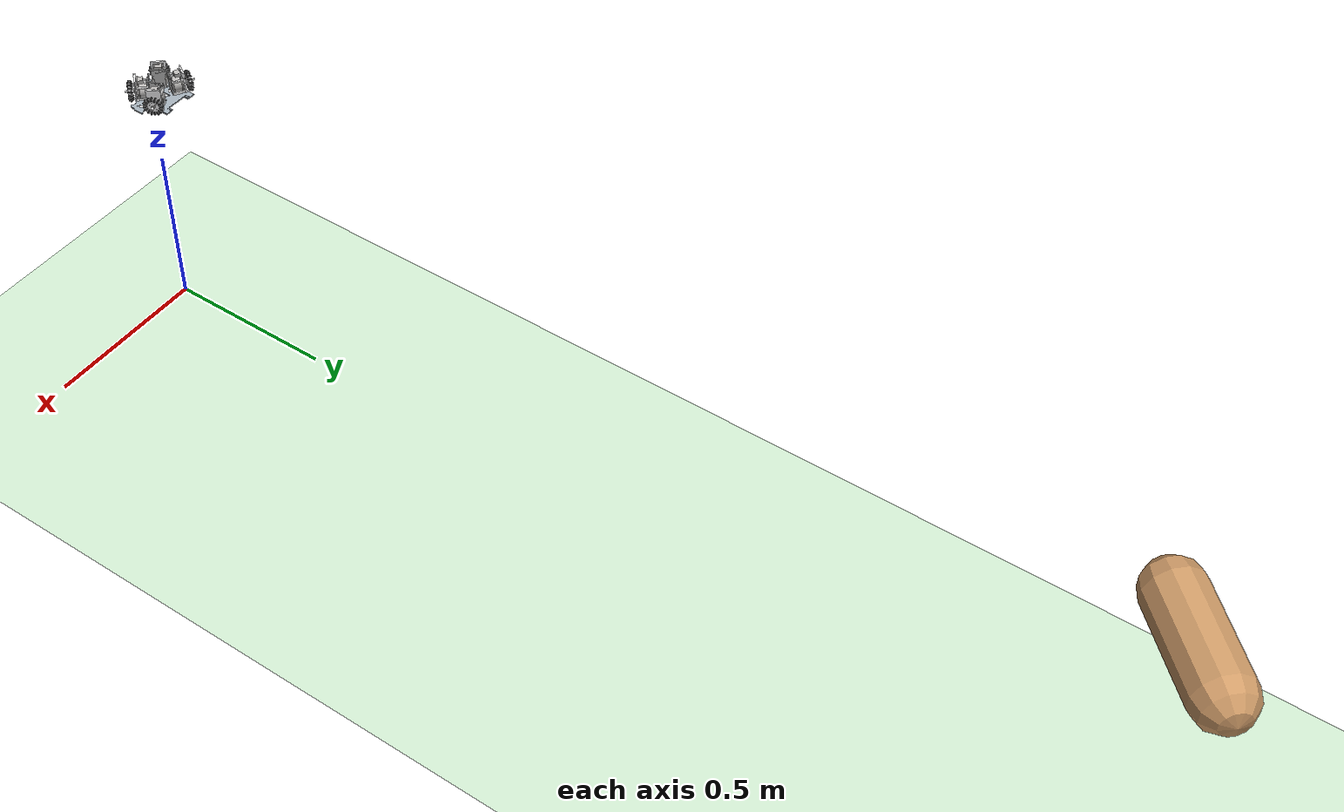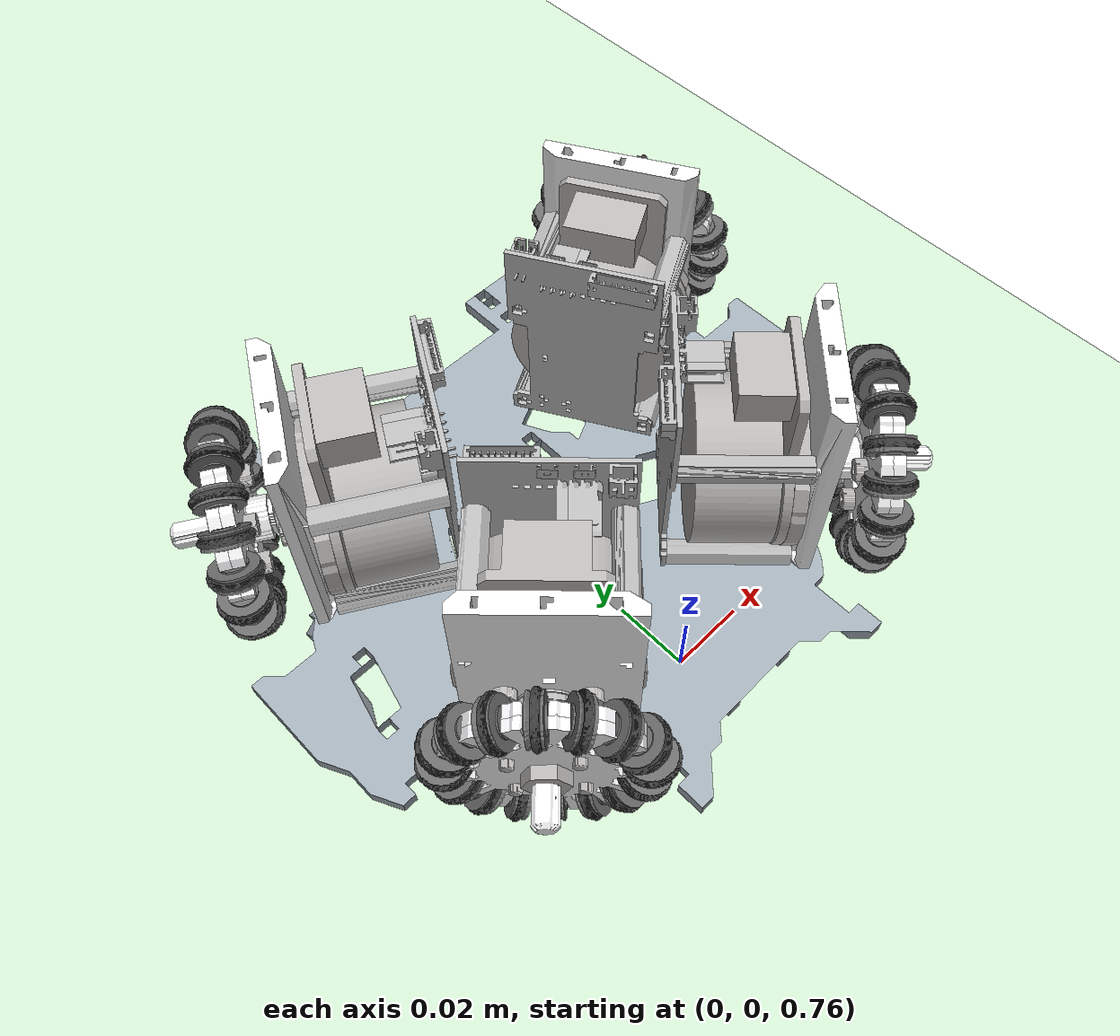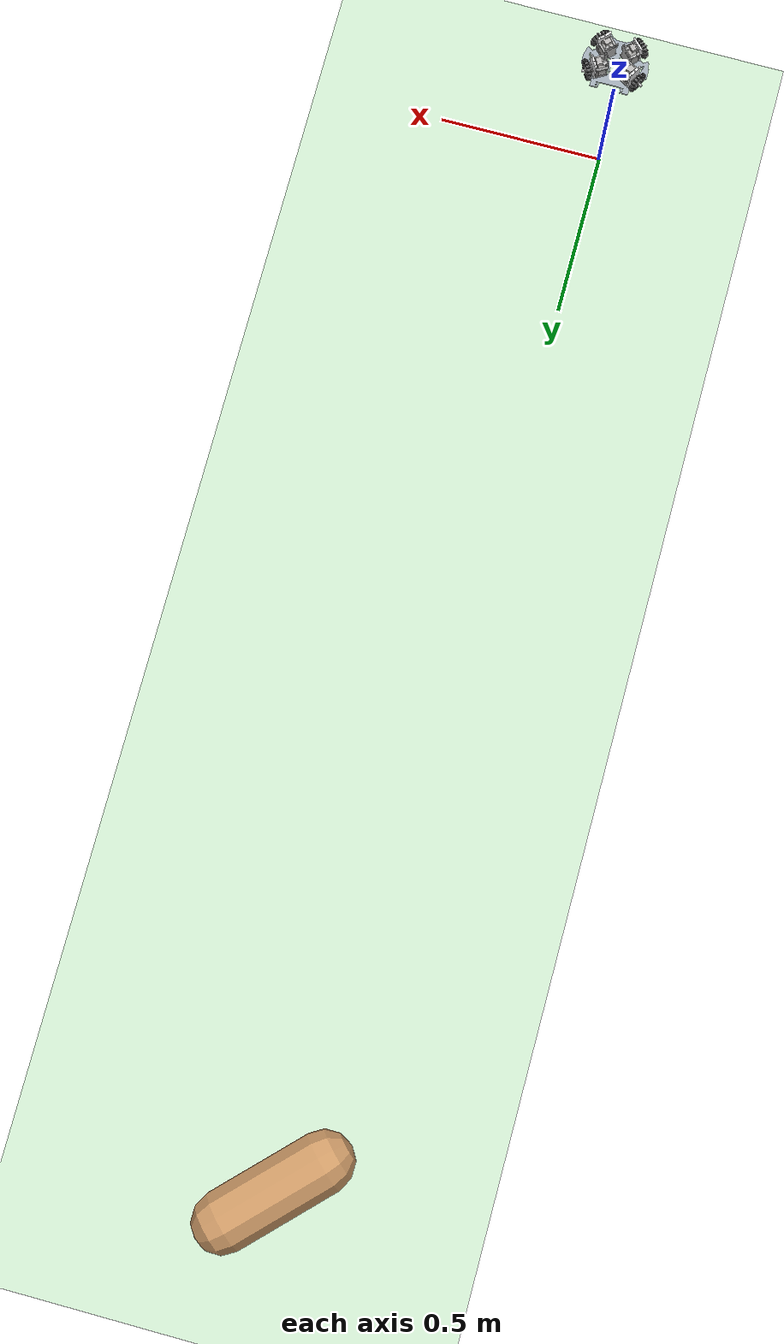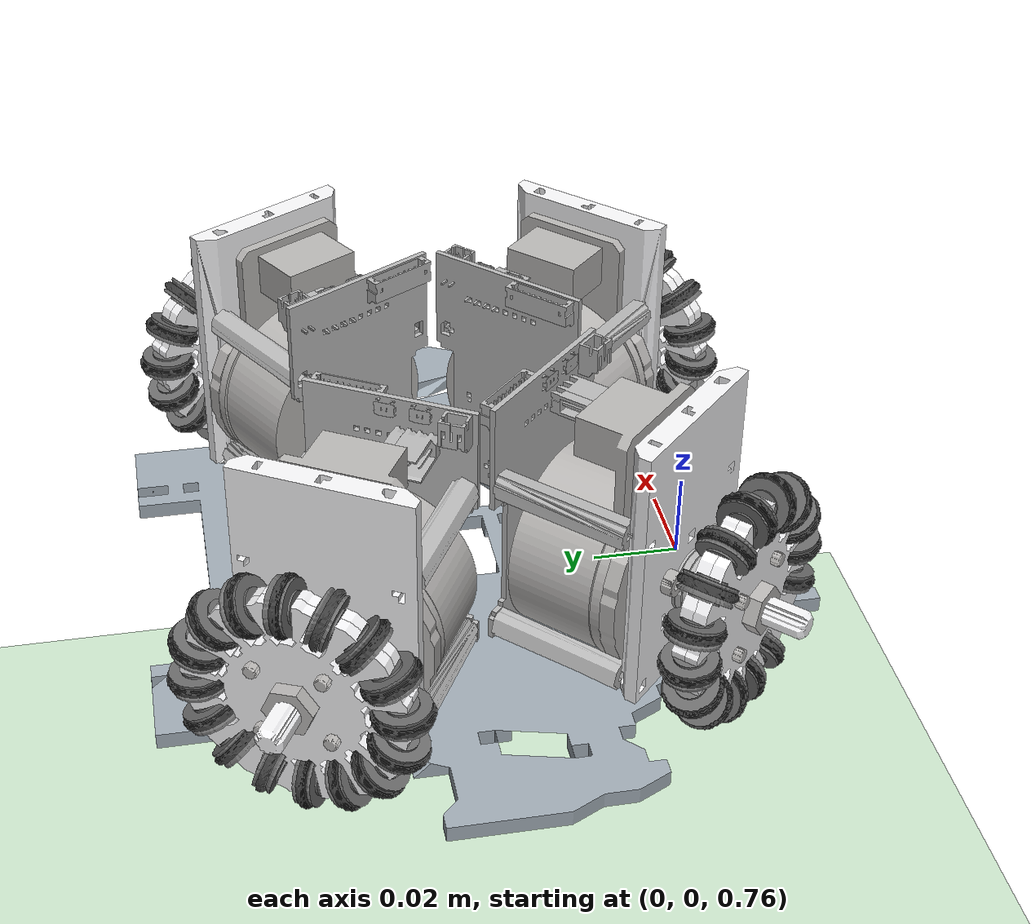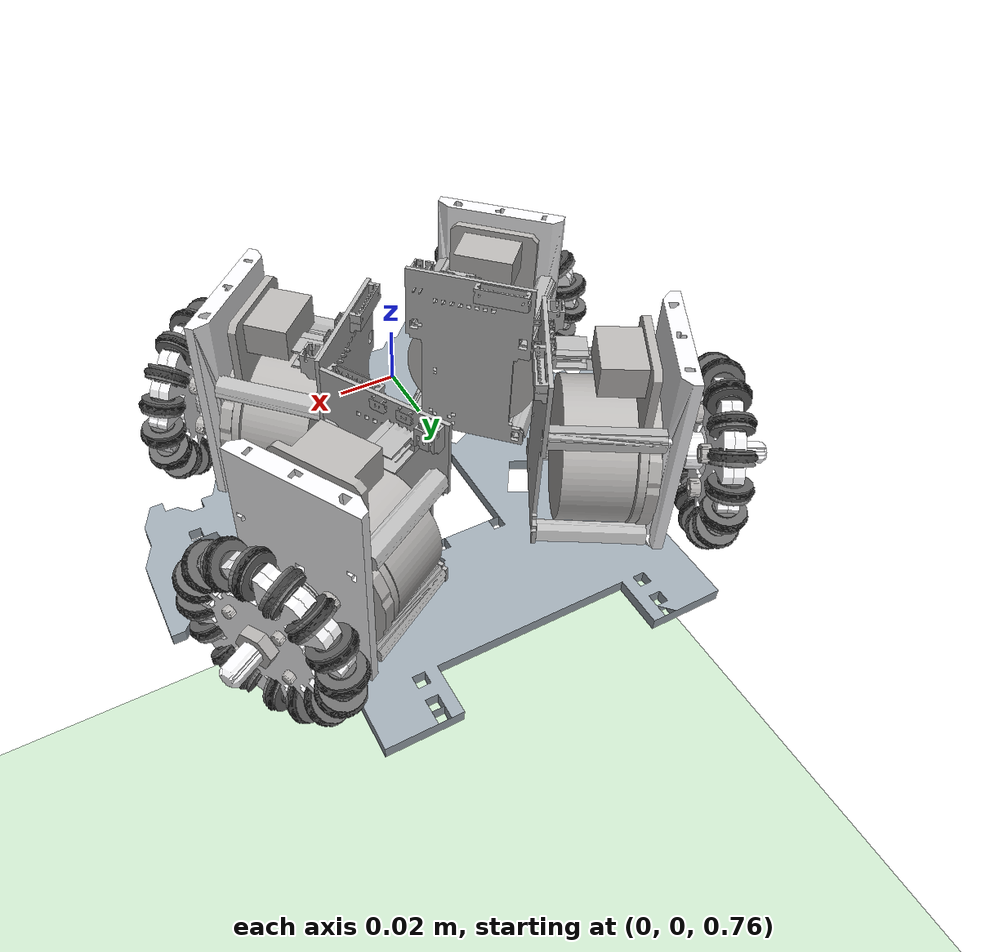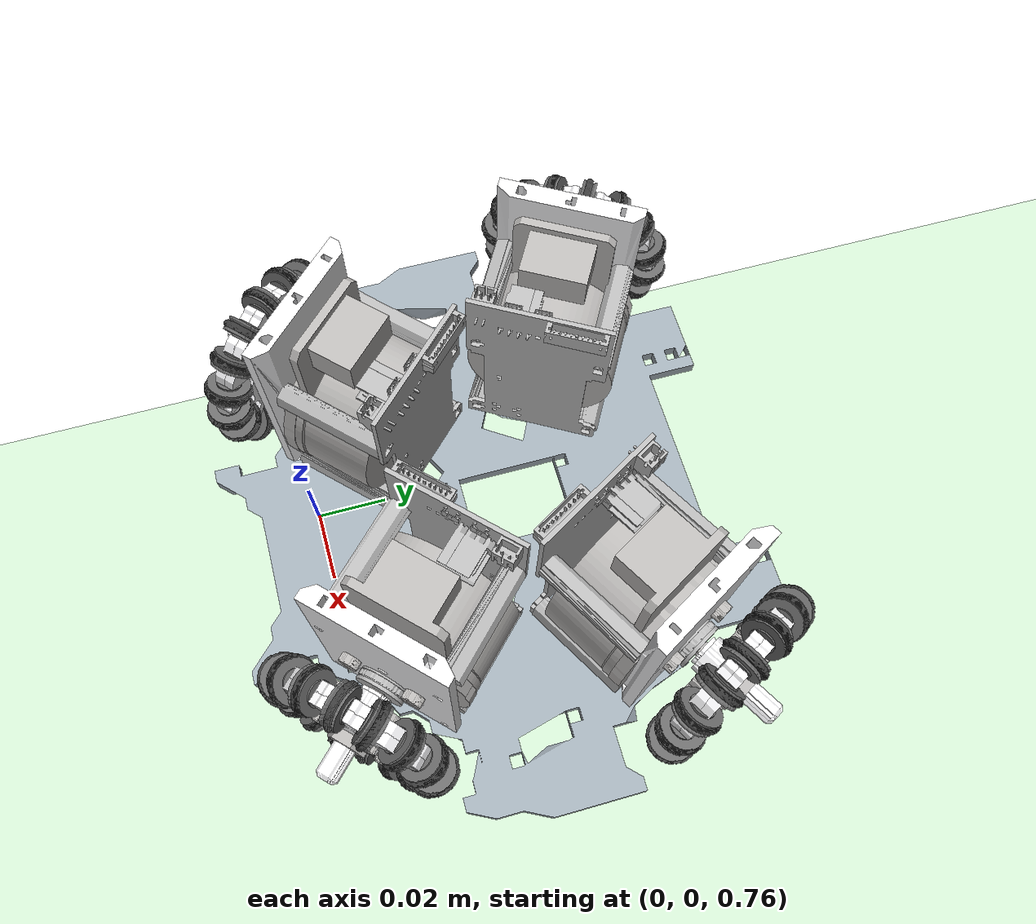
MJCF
<mujoco model="onshape">
    <compiler angle="degree" coordinate="local" inertiafromgeom="true" />
    <option integrator="RK4" timestep="0.01" gravity="0 0 -9.81" />

    <default>
        <geom conaffinity="0" condim="3" density="5.0" friction="1 0.5 0.5" margin="0.01"
            rgba="0.8 0.6 0.4 1" />
    </default>

    <asset>
        <mesh name="part_1" file="part_1.stl" />
        <mesh name="part_27" file="part_27.stl" />
        <mesh name="lbmfn3-32_r:1" file="lbmfn3-32_r:1.stl" />
        <mesh name="brushless3301.step_19" file="brushless3301.step_19.stl" />
        <mesh name="as_1420_-_metric_m3_x_8:1" file="as_1420_-_metric_m3_x_8:1.stl" />
        <mesh name="brushless3285.step_18" file="brushless3285.step_18.stl" />
        <mesh name="wheel_fix_plate_collet:1" file="wheel_fix_plate_collet:1.stl" />
        <mesh name="core_ba0414:1" file="core_ba0414:1.stl" />
        <mesh name="brushless3324.step_20" file="brushless3324.step_20.stl" />
        <mesh name="brushless3251.step_15" file="brushless3251.step_15.stl" />
        <mesh name="maxon_ec45_70w:1_(1)" file="maxon_ec45_70w:1_(1).stl" />
        <mesh name="brushless3272.step_17" file="brushless3272.step_17.stl" />
        <mesh name="brushless3249.step_14" file="brushless3249.step_14.stl" />
        <mesh name="washer_ba0414:1" file="washer_ba0414:1.stl" />
        <mesh name="brushless3169.step_13" file="brushless3169.step_13.stl" />
        <mesh name="part_28" file="part_28.stl" />
        <mesh name="spwf3:1" file="spwf3:1.stl" />
        <mesh name="oring_od13:1" file="oring_od13:1.stl" />
        <mesh name="szv3-12:1" file="szv3-12:1.stl" />
        <mesh name="3_8_axis:1" file="3_8_axis:1.stl" />
        <mesh name="collet_nut:1" file="collet_nut:1.stl" />
        <mesh name="collet_screw:1" file="collet_screw:1.stl" />
        <mesh name="as_1474_-_metric_m6:1" file="as_1474_-_metric_m6:1.stl" />
        <mesh name="plate1_m6collet:1" file="plate1_m6collet:1.stl" />
        <mesh name="plate1_3mm_m6collet:1" file="plate1_3mm_m6collet:1.stl" />

        <texture builtin="gradient" height="100" rgb1="1 1 1" rgb2="0 0 0" type="skybox" width="100" />
        <texture builtin="flat" height="1278" mark="cross" markrgb="1 1 1" name="texgeom"
            random="0.01"
            rgb1="0.8 0.6 0.4" rgb2="0.8 0.6 0.4" type="cube" width="127" />
        <texture builtin="checker" height="100" name="texplane" rgb1="0 0 0" rgb2="0.8 0.8 0.8"
            type="2d" width="100" />
        <material name="MatPlane" reflectance="0.5" shininess="1" specular="1" texrepeat="60 60"
            texture="texplane" />
        <material name="geom" texture="texgeom" texuniform="true" />
    </asset>
    <worldbody>
        <light cutoff="100" diffuse="1 1 1" dir="-0 0 -1.3" directional="true" exponent="1"
            pos="0 0 1.3" specular=".1 .1 .1" />
        <geom conaffinity="1" condim="3" material="MatPlane" name="floor" pos="0 0 0"
            rgba="0.8 0.9 0.8 1" size="40 40 40" type="plane" />

        <body name="yeet" pos="0 3 0.75">
            <geom fromto="0.0 0.0 0.0 0.2 0.2 0.0" name="aux_1_geom" size="0.08" type="capsule" />
        </body>

        <body name="robot" pos="0 0 0.75">

            <camera name="track" mode="trackcom" pos="0
    -1 0.3" xyaxes="1 0 0 0 0 1" />
            <geom pos="0.010763 0.0557072 0.00576549" type="mesh"
                rgba="0.623529 0.666667 0.701961 1"
                mesh="part_1" />
            <geom pos="-0.0323705
    0.0125736 0.0312655"
                quat="-0.653281 -0.270596 0.653283 -0.270598"
                type="mesh"
                rgba="0.717647 0.709804 0.701961 1" mesh="part_27" />
            <geom pos="-0.0217639 0.0472218
    0.0512656"
                quat="-0.0183875 -0.38224 0.922813 0.0443951"
                type="mesh" rgba="0.717647
    0.717647 0.717647 1" mesh="lbmfn3-32_r:1" />
            <geom pos="0.0286519 -0.00206445 -0.0501114"
                quat="-0.2706 -0.270598 -0.653279 -0.653283"
                type="mesh" rgba="0.717647 0.717647
    0.717647 1" mesh="brushless3301.step_19" />
            <geom pos="-0.035906 0.00903811 0.0202655"
                quat="-0.653282 -0.65328 -0.270598 -0.270601"
                type="mesh" rgba="0.717647 0.709804
    0.701961 1" mesh="as_1420_-_metric_m3_x_8:1" />
            <geom pos="0.0286519 -0.00206445
    -0.0501114"
                quat="-0.2706 -0.270598 -0.653279 -0.653283"
                type="mesh" rgba="0.717647
    0.717647 0.717647 1" mesh="brushless3285.step_18" />
            <geom pos="-0.0292359 0.00223603
    0.0367655"
                quat="5.0774e-07 -0.923879 -0.382685 -1.2258e-06"
                type="mesh" rgba="0.717647
    0.709804 0.701961 1" mesh="as_1420_-_metric_m3_x_8:1" />
            <geom pos="-0.0323705 0.0125736
    0.0237655"
                quat="-0.653282 -0.653281 0.270598 0.270598"
                type="mesh" rgba="0.956863
    0.956863 0.964706 1" mesh="wheel_fix_plate_collet:1" />
            <geom pos="-0.0373202 0.00762388
    0.0312655"
                quat="-0.669252 -0.63691 -0.263817 -0.277216"
                type="mesh" rgba="0.717647
    0.717647 0.717647 1" mesh="core_ba0414:1" />
            <geom pos="0.0286519 -0.00206445 -0.0501114"
                quat="-0.2706 -0.270598 -0.653279 -0.653283"
                type="mesh" rgba="0.717647 0.717647
    0.717647 1" mesh="brushless3324.step_20" />
            <geom pos="0.00227779 0.0231803 0.0127656"
                quat="-0.370626 -0.0952978 0.230067 0.894776"
                type="mesh" rgba="0.717647 0.717647
    0.717647 1" mesh="lbmfn3-32_r:1" />
            <geom pos="0.0286519 -0.00206445 -0.0501114"
                quat="-0.2706 -0.270598 -0.653279 -0.653283"
                type="mesh" rgba="0.717647 0.717647
    0.717647 1" mesh="brushless3251.step_15" />
            <geom pos="-0.0426421 0.0157742 0.0367655"
                quat="-0.653282 -0.65328 -0.270598 -0.270601"
                type="mesh" rgba="0.717647 0.709804
    0.701961 1" mesh="as_1420_-_metric_m3_x_8:1" />
            <geom pos="-0.0327193 0.0122248 0.0312655"
                quat="-0.653281 -0.270596 0.653283 -0.270598"
                type="mesh" rgba="0.717647 0.709804
    0.701961 1" mesh="maxon_ec45_70w:1_(1)" />
            <geom pos="0.00227772 0.0231802 0.0512656"
                quat="-0.0730178 -0.375651 0.906906 0.176285"
                type="mesh" rgba="0.717647 0.717647
    0.717647 1" mesh="lbmfn3-32_r:1" />
            <geom pos="0.0286519 -0.00206445 -0.0501114"
                quat="-0.2706 -0.270598 -0.653279 -0.653283"
                type="mesh" rgba="0.717647 0.717647
    0.717647 1" mesh="brushless3272.step_17" />
            <geom pos="0.0286519 -0.00206445 -0.0501114"
                quat="-0.2706 -0.270598 -0.653279 -0.653283"
                type="mesh" rgba="0.717647 0.717647
    0.717647 1" mesh="brushless3249.step_14" />
            <geom pos="-0.0383809 0.00656322 0.0312655"
                quat="-0.669252 -0.63691 -0.263817 -0.277216"
                type="mesh" rgba="0.717647 0.717647
    0.717647 1" mesh="washer_ba0414:1" />
            <geom pos="0.0286519 -0.00206445 -0.0501114"
                quat="-0.2706 -0.270598 -0.653279 -0.653283"
                type="mesh" rgba="0.717647 0.717647
    0.717647 1" mesh="brushless3169.step_13" />
            <geom pos="-0.0362596 0.00868454 0.0312655"
                quat="0.277213 -0.263815 0.636911 -0.669253"
                type="mesh" rgba="0.717647 0.717647
    0.717647 1" mesh="washer_ba0414:1" />
            <geom pos="-0.0217638 0.0472219 0.0127656"
                quat="0.220435 -0.312816 0.755211 -0.532176"
                type="mesh" rgba="0.717647 0.717647
    0.717647 1" mesh="lbmfn3-32_r:1" />
            <geom pos="-0.0327193 0.0122248 0.0312655"
                quat="-0.653281 -0.270596 0.653283 -0.270598"
                type="mesh" rgba="0.717647 0.709804
    0.701961 1" mesh="part_28" />
            <geom pos="0.0642341 0.0157083 0.0367655"
                quat="1.2258e-06
    0.382682 0.92388 -5.07745e-07"
                type="mesh" rgba="0.717647 0.709804 0.701961 1"
                mesh="as_1420_-_metric_m3_x_8:1" />
            <geom pos="0.0192482 0.0231804 0.0512654"
                quat="0.044395 0.922812 -0.382243 -0.0183877"
                type="mesh" rgba="0.717647 0.717647
    0.717647 1" mesh="lbmfn3-32_r:1" />
            <geom pos="0.0685349 0.0735957 -0.0501116"
                quat="-0.270597 -0.270597 0.653282 0.653282"
                type="mesh" rgba="0.717647 0.717647
    0.717647 1" mesh="brushless3301.step_19" />
            <geom pos="0.057432 0.00903815 0.0202655"
                quat="0.270598 0.270596 0.653281 0.653283"
                type="mesh"
                rgba="0.717647 0.709804
    0.701961 1" mesh="as_1420_-_metric_m3_x_8:1" />
            <geom pos="0.0599069 0.0065633 0.0312655"
                quat="0.277213 0.263815 0.636911 0.669253"
                type="mesh"
                rgba="0.717647 0.717647
    0.717647 1" mesh="washer_ba0414:1" />
            <geom pos="0.0538965 0.0125737 0.0312655"
                quat="0.270598 0.65328 -0.2706 0.653282" type="mesh"
                rgba="0.717647 0.709804 0.701961 1"
                mesh="part_27" />
            <geom pos="0.0685349 0.0735957 -0.0501116"
                quat="-0.270597 -0.270597
    0.653282 0.653282"
                type="mesh" rgba="0.717647 0.717647 0.717647 1"
                mesh="brushless3324.step_20" />
            <geom pos="0.0506959 0.00230209 0.0367655"
                quat="0.270598
    0.270596 0.653281 0.653283"
                type="mesh" rgba="0.717647 0.709804 0.701961 1"
                mesh="as_1420_-_metric_m3_x_8:1" />
            <geom pos="0.0685349 0.0735957 -0.0501116"
                quat="-0.270597 -0.270597 0.653282 0.653282"
                type="mesh" rgba="0.717647 0.717647
    0.717647 1" mesh="brushless3285.step_18" />
            <geom pos="0.0588462 0.00762396 0.0312655"
                quat="0.277213 0.263815 0.636911 0.669253"
                type="mesh" rgba="0.717647 0.717647 0.717647
    1" mesh="core_ba0414:1" />
            <geom pos="0.0432899 0.0472219 0.0127654"
                quat="0.894775
    0.230067 -0.0952986 -0.370629"
                type="mesh" rgba="0.717647 0.717647 0.717647 1"
                mesh="lbmfn3-32_r:1" />
            <geom pos="0.0538965 0.0125737 0.0237655" quat="0.653284 0.653279
    0.270597 0.270599"
                type="mesh"
                rgba="0.956863 0.956863 0.964706 1"
                mesh="wheel_fix_plate_collet:1" />
            <geom pos="0.0542453 0.0122249 0.0312655"
                quat="0.270598 0.65328 -0.2706 0.653282" type="mesh"
                rgba="0.717647 0.709804 0.701961 1"
                mesh="maxon_ec45_70w:1_(1)" />
            <geom pos="0.0685349 0.0735957 -0.0501116"
                quat="-0.270597
    -0.270597 0.653282 0.653282"
                type="mesh" rgba="0.717647 0.717647 0.717647 1"
                mesh="brushless3251.step_15" />
            <geom pos="0.0685349 0.0735957 -0.0501116"
                quat="-0.270597
    -0.270597 0.653282 0.653282"
                type="mesh" rgba="0.717647 0.717647 0.717647 1"
                mesh="brushless3249.step_14" />
            <geom pos="0.0432899 0.047222 0.0512654"
                quat="0.176285
    0.906904 -0.375654 -0.0730185"
                type="mesh" rgba="0.717647 0.717647 0.717647 1"
                mesh="lbmfn3-32_r:1" />
            <geom pos="0.0685349 0.0735957 -0.0501116"
                quat="-0.270597
    -0.270597 0.653282 0.653282"
                type="mesh" rgba="0.717647 0.717647 0.717647 1"
                mesh="brushless3169.step_13" />
            <geom pos="0.0685349 0.0735957 -0.0501116"
                quat="-0.270597
    -0.270597 0.653282 0.653282"
                type="mesh" rgba="0.717647 0.717647 0.717647 1"
                mesh="brushless3272.step_17" />
            <geom pos="0.0542453 0.0122249 0.0312655" quat="0.270598
    0.65328 -0.2706 0.653282"
                type="mesh"
                rgba="0.717647 0.709804 0.701961 1" mesh="part_28"
            />
            <geom pos="0.0577856 0.00868462 0.0312655" quat="-0.669252 0.63691 -0.263817 0.277216"
                type="mesh" rgba="0.717647 0.717647 0.717647 1" mesh="washer_ba0414:1" />
            <geom
                pos="0.0192483 0.0231803 0.0127654" quat="-0.532175 0.75521 -0.312819 0.220436"
                type="mesh"
                rgba="0.717647 0.717647 0.717647 1" mesh="lbmfn3-32_r:1" />
            <geom pos="0.0679207 0.0887072
    0.0202655"
                quat="-0.183015 -0.183016 0.68301 0.683013"
                type="mesh" rgba="0.717647
    0.709804 0.701961 1" mesh="as_1420_-_metric_m3_x_8:1" />
            <geom pos="0.0683537 0.0889572
    0.0312655"
                quat="-0.699711 0.665896 0.178428 -0.187487"
                type="mesh" rgba="0.717647
    0.717647 0.717647 1" mesh="washer_ba0414:1" />
            <geom pos="0.00843638 0.11614 -0.0501116"
                quat="-0.612373 -0.612373 0.353553 0.353553"
                type="mesh" rgba="0.717647 0.717647
    0.717647 1" mesh="brushless3169.step_13" />
            <geom pos="0.0709518 0.0904572 0.0312655"
                quat="-0.187489 -0.17843 0.665895 0.69971"
                type="mesh"
                rgba="0.717647 0.717647
    0.717647 1" mesh="washer_ba0414:1" />
            <geom pos="0.0635906 0.0862072 0.0312655"
                quat="-0.183015 0.683012 0.183012 0.683013"
                type="mesh" rgba="0.717647 0.709804 0.701961
    1" mesh="part_27" />
            <geom pos="0.00843638 0.11614 -0.0501116"
                quat="-0.612373 -0.612373
    0.353553 0.353553"
                type="mesh" rgba="0.717647 0.717647 0.717647 1"
                mesh="brushless3324.step_20" />
            <geom pos="0.00843638 0.11614 -0.0501116"
                quat="-0.612373
    -0.612373 0.353553 0.353553"
                type="mesh" rgba="0.717647 0.717647 0.717647 1"
                mesh="brushless3285.step_18" />
            <geom pos="0.00843638 0.11614 -0.0501116"
                quat="-0.612373
    -0.612373 0.353553 0.353553"
                type="mesh" rgba="0.717647 0.717647 0.717647 1"
                mesh="brushless3301.step_19" />
            <geom pos="0.044378 0.0554847 0.0127654" quat="-0.556396
    0.78958 0.211569 -0.149085"
                type="mesh"
                rgba="0.717647 0.717647 0.717647 1"
                mesh="lbmfn3-32_r:1" />
            <geom pos="0.0696528 0.0897072 0.0312655" quat="-0.187489 -0.17843
    0.665895 0.69971"
                type="mesh"
                rgba="0.717647 0.717647 0.717647 1"
                mesh="core_ba0414:1" />
            <geom pos="0.0640178 0.0864538 0.0312655"
                quat="-0.183015 0.683012
    0.183012 0.683013"
                type="mesh" rgba="0.717647 0.709804 0.701961 1"
                mesh="maxon_ec45_70w:1_(1)" />
            <geom pos="0.00843638 0.11614 -0.0501116"
                quat="-0.612373
    -0.612373 0.353553 0.353553"
                type="mesh" rgba="0.717647 0.717647 0.717647 1"
                mesh="brushless3249.step_14" />
            <geom pos="0.00843638 0.11614 -0.0501116"
                quat="-0.612373
    -0.612373 0.353553 0.353553"
                type="mesh" rgba="0.717647 0.717647 0.717647 1"
                mesh="brushless3251.step_15" />
            <geom pos="0.0726839 0.0804572 0.0367655"
                quat="-0.183015
    -0.183016 0.68301 0.683013"
                type="mesh" rgba="0.717647 0.709804 0.701961 1"
                mesh="as_1420_-_metric_m3_x_8:1" />
            <geom pos="0.0273777 0.0849294 0.0512654"
                quat="0.184307 0.948179 0.254064 0.0493863"
                type="mesh" rgba="0.717647 0.717647 0.717647
    1" mesh="lbmfn3-32_r:1" />
            <geom pos="0.0273778 0.0849294 0.0127654"
                quat="0.935497
    0.240538 0.0644508 0.250667"
                type="mesh" rgba="0.717647 0.717647 0.717647 1"
                mesh="lbmfn3-32_r:1" />
            <geom pos="0.0632383 0.0970038 0.0367655"
                quat="1.28159e-06
    -0.258823 0.965925 3.43401e-07"
                type="mesh" rgba="0.717647 0.709804 0.701961 1"
                mesh="as_1420_-_metric_m3_x_8:1" />
            <geom pos="0.0640178 0.0864538 0.0312655"
                quat="-0.183015 0.683012 0.183012 0.683013"
                type="mesh" rgba="0.717647 0.709804 0.701961
    1" mesh="part_28" />
            <geom pos="0.00843638 0.11614 -0.0501116"
                quat="-0.612373 -0.612373
    0.353553 0.353553"
                type="mesh" rgba="0.717647 0.717647 0.717647 1"
                mesh="brushless3272.step_17" />
            <geom pos="0.0443779 0.0554846 0.0512654"
                quat="0.0464146
    0.96481 0.258521 0.0124382"
                type="mesh" rgba="0.717647 0.717647 0.717647 1"
                mesh="lbmfn3-32_r:1" />
            <geom pos="0.0635906 0.0862072 0.0237655" quat="0.353553 0.353551
    0.612371 0.612375"
                type="mesh"
                rgba="0.956863 0.956863 0.964706 1"
                mesh="wheel_fix_plate_collet:1" />
            <geom pos="-0.0404107 0.0234757 -0.0501116"
                quat="0.612374 0.612373 0.353551 0.353551"
                type="mesh" rgba="0.717647 0.717647 0.717647
    1" mesh="brushless3249.step_14" />
            <geom pos="-0.00585173 0.0849294 0.0127654"
                quat="0.149089 -0.21157 -0.789579 0.556395"
                type="mesh" rgba="0.717647 0.717647 0.717647
    1" mesh="lbmfn3-32_r:1" />
            <geom pos="-0.0463946 0.0887072 0.0202655"
                quat="0.683014
    0.683012 -0.183012 -0.183014"
                type="mesh" rgba="0.717647 0.709804 0.701961 1"
                mesh="as_1420_-_metric_m3_x_8:1" />
            <geom pos="-0.0424917 0.0864538 0.0312655"
                quat="0.683013 -0.183017 -0.683011 -0.183015"
                type="mesh" rgba="0.717647 0.709804
    0.701961 1" mesh="maxon_ec45_70w:1_(1)" />
            <geom pos="-0.0404107 0.0234757 -0.0501116"
                quat="0.612374 0.612373 0.353551 0.353551"
                type="mesh" rgba="0.717647 0.717647 0.717647
    1" mesh="brushless3272.step_17" />
            <geom pos="-0.0404107 0.0234757 -0.0501116"
                quat="0.612374 0.612373 0.353551 0.353551"
                type="mesh" rgba="0.717647 0.717647 0.717647
    1" mesh="brushless3324.step_20" />
            <geom pos="-0.0404107 0.0234757 -0.0501116"
                quat="0.612374 0.612373 0.353551 0.353551"
                type="mesh" rgba="0.717647 0.717647 0.717647
    1" mesh="brushless3251.step_15" />
            <geom pos="-0.0468276 0.0889572 0.0312655"
                quat="0.187491 -0.178428 -0.665895 0.69971"
                type="mesh" rgba="0.717647 0.717647 0.717647
    1" mesh="washer_ba0414:1" />
            <geom pos="-0.0416314 0.0969572 0.0367655"
                quat="0.683014
    0.683012 -0.183012 -0.183014"
                type="mesh" rgba="0.717647 0.709804 0.701961 1"
                mesh="as_1420_-_metric_m3_x_8:1" />
            <geom pos="-0.0481267 0.0897072 0.0312655"
                quat="0.699711 0.665896 -0.178426 -0.187488"
                type="mesh" rgba="0.717647 0.717647
    0.717647 1" mesh="core_ba0414:1" />
            <geom pos="-0.0512386 0.0805038 0.0367655"
                quat="-3.43405e-07 0.965926 -0.25882 -1.28158e-06"
                type="mesh" rgba="0.717647 0.709804
    0.701961 1" mesh="as_1420_-_metric_m3_x_8:1" />
            <geom pos="-0.0404107 0.0234757
    -0.0501116"
                quat="0.612374 0.612373 0.353551 0.353551"
                type="mesh" rgba="0.717647
    0.717647 0.717647 1" mesh="brushless3285.step_18" />
            <geom pos="-0.0424917 0.0864538
    0.0312655"
                quat="0.683013 -0.183017 -0.683011 -0.183015"
                type="mesh" rgba="0.717647
    0.709804 0.701961 1" mesh="part_28" />
            <geom pos="-0.0404107 0.0234757 -0.0501116"
                quat="0.612374 0.612373 0.353551 0.353551"
                type="mesh" rgba="0.717647 0.717647 0.717647
    1" mesh="brushless3301.step_19" />
            <geom pos="-0.0228518 0.0554846 0.0512654"
                quat="-0.0493845 -0.254068 -0.948178 -0.184307"
                type="mesh" rgba="0.717647 0.717647
    0.717647 1" mesh="lbmfn3-32_r:1" />
            <geom pos="-0.00585164 0.0849294 0.0512654"
                quat="-0.0124358 -0.258524 -0.964809 -0.0464152"
                type="mesh" rgba="0.717647 0.717647
    0.717647 1" mesh="lbmfn3-32_r:1" />
            <geom pos="-0.0420645 0.0862072 0.0312655"
                quat="0.683013 -0.183017 -0.683011 -0.183015"
                type="mesh" rgba="0.717647 0.709804
    0.701961 1" mesh="part_27" />
            <geom pos="-0.0228519 0.0554847 0.0127654"
                quat="-0.250669
    -0.0644542 -0.240537 -0.935496"
                type="mesh" rgba="0.717647 0.717647 0.717647 1"
                mesh="lbmfn3-32_r:1" />
            <geom pos="-0.0404107 0.0234757 -0.0501116"
                quat="0.612374
    0.612373 0.353551 0.353551"
                type="mesh" rgba="0.717647 0.717647 0.717647 1"
                mesh="brushless3169.step_13" />
            <geom pos="-0.0494257 0.0904572 0.0312655"
                quat="0.699711
    0.665896 -0.178426 -0.187488"
                type="mesh" rgba="0.717647 0.717647 0.717647 1"
                mesh="washer_ba0414:1" />
            <geom pos="-0.0420645 0.0862072 0.0237655"
                quat="0.353553
    0.353551 -0.612371 -0.612375"
                type="mesh" rgba="0.956863 0.956863 0.964706 1"
                mesh="wheel_fix_plate_collet:1" />
            <body name="wheel" pos="-0.0468614 -0.00191733
    0.0312654"
                quat="0.270598 -0.65328 -0.2706 -0.653282">
                <inertial pos="0 0 0"
                    quat="0.00194869 0.707104 -0.000189537 0.707107" mass="0.5"
                    diaginertia="0.000357205
    0.000221873 0.000135501" />
                <joint name="wheel_0" pos="0 0 0" axis="0 0 1" />
                <geom
                    pos="-0.00709855 0.00840301 0.00475" quat="0.159914 0.688786 0.159914 -0.688788"
                    type="mesh"
                    rgba="0.717647 0.709804 0.701961 1" mesh="as_1420_-_metric_m3_x_8:1" />
                <geom
                    pos="-0.000426961 0.0226531 0.00175"
                    quat="0.0418681 0.00283513 0.0675015 0.996836"
                    type="mesh"
                    rgba="0.423529 0.423529 0.423529 1" mesh="spwf3:1" />
                <geom pos="-0.00161731 -0.0224811
    0.00175"
                    quat="0.0418816 -0.00262812 -0.0625728 0.997158"
                    type="mesh" rgba="0.235294
    0.235294 0.235294 1" mesh="oring_od13:1" />
                <geom pos="-0.0147529 0.0170401 0.00175"
                    quat="0.937281 -0.0588155 -0.0215175 0.342902"
                    type="mesh" rgba="0.235294 0.235294
    0.235294 1" mesh="oring_od13:1" />
                <geom pos="-0.0221327 -0.0047762 0.00175"
                    quat="0.805489 0.0558545 -0.0408121 -0.588559"
                    type="mesh" rgba="0.423529 0.423529
    0.423529 1" mesh="spwf3:1" />
                <geom pos="-0.00405719 -0.0222757 0.00175"
                    quat="0.996726
    0.0691153 -0.00290289 -0.0418632"
                    type="mesh" rgba="0.423529 0.423529 0.423529 1"
                    mesh="spwf3:1" />
                <geom pos="0.0200598 -0.0102737 0.00175"
                    quat="0.852279 0.0549679
    0.0334803 0.519113"
                    type="mesh" rgba="0.423529 0.423529 0.423529 1" mesh="szv3-12:1"
                />
                <geom pos="0.000426961 -0.0226531 0.00175"
                    quat="0.996836 0.0675015 -0.00283511
    -0.0418679"
                    type="mesh" rgba="0.423529 0.423529 0.423529 1" mesh="spwf3:1" />
                <geom
                    pos="-0.0186202 -0.0128825 0.00175"
                    quat="0.904834 0.0627433 -0.0291312 -0.420107"
                    type="mesh"
                    rgba="0.423529 0.423529 0.423529 1" mesh="spwf3:1" />
                <geom pos="0.00181511 0.0224644
    0.00175"
                    quat="0.041877 0.00270087 0.0643048 0.997048"
                    type="mesh" rgba="0.423529
    0.423529 0.423529 1" mesh="szv3-12:1" />
                <geom pos="0.0226645 0.00310895 0.00175"
                    quat="-0.353469 0.522845 -0.476061 -0.612421"
                    type="mesh" rgba="0.960784 0.960784
    0.960784 1" mesh="3_8_axis:1" />
                <geom pos="0.0201509 -0.0100973 0.00175"
                    quat="0.519167
    -0.0325783 0.0534875 -0.852375"
                    type="mesh" rgba="0.235294 0.235294 0.235294 1"
                    mesh="oring_od13:1" />
                <geom pos="0.00161731 0.0224811 0.00175"
                    quat="0.997158
    -0.0625728 0.00262811 -0.0418814"
                    type="mesh" rgba="0.235294 0.235294 0.235294 1"
                    mesh="oring_od13:1" />
                <geom pos="0.00310895 -0.0226645 0.00175"
                    quat="0.682987
    -0.0330819 0.706333 0.183107"
                    type="mesh" rgba="0.960784 0.960784 0.960784 1"
                    mesh="3_8_axis:1" />
                <geom pos="0.0146013 -0.0171682 0.00175"
                    quat="0.937177 0.0604434
    0.0221131 0.342865"
                    type="mesh" rgba="0.423529 0.423529 0.423529 1" mesh="szv3-12:1"
                />
                <geom pos="-0.00580103 -0.022129 0.00175"
                    quat="0.705586 0.105353 0.699215 0.0463446"
                    type="mesh" rgba="0.960784 0.960784 0.960784 1" mesh="3_8_axis:1" />
                <geom
                    pos="-0.0163201 0.0157162 0.00175" quat="0.34279 0.0232123 -0.0634482 -0.936979"
                    type="mesh"
                    rgba="0.423529 0.423529 0.423529 1" mesh="spwf3:1" />
                <geom pos="-0.0128825 0.0186202
    0.00175"
                    quat="0.342752 0.0237672 -0.0649651 -0.936875"
                    type="mesh" rgba="0.423529
    0.423529 0.423529 1" mesh="spwf3:1" />
                <geom pos="-0.0146013 0.0171682 0.00175"
                    quat="0.342863 0.022113 -0.0604435 -0.937178"
                    type="mesh" rgba="0.423529 0.423529
    0.423529 1" mesh="szv3-12:1" />
                <geom pos="0.0182246 -0.0138279 0.00175"
                    quat="0.560925
    -0.300866 0.639906 0.430538"
                    type="mesh" rgba="0.960784 0.960784 0.960784 1"
                    mesh="3_8_axis:1" />
                <geom pos="0.0207653 0.00906342 0.00175"
                    quat="0.588626 0.0398592
    0.0545503 0.805578"
                    type="mesh" rgba="0.423529 0.423529 0.423529 1" mesh="spwf3:1" />
                <geom pos="0.0115456 -0.0197495 0.00175" quat="0.634141 -0.170245 0.686307 0.312834"
                    type="mesh"
                    rgba="0.960784 0.960784 0.960784 1" mesh="3_8_axis:1" />
                <geom pos="-0.00181511
    -0.0224644 0.00175"
                    quat="0.997048 0.0643048 -0.00270085 -0.0418768"
                    type="mesh"
                    rgba="0.423529 0.423529 0.423529 1" mesh="szv3-12:1" />
                <geom pos="-0.0170401 -0.0147529
    0.00175"
                    quat="0.42029 -0.0263737 -0.056804 0.905226"
                    type="mesh" rgba="0.235294
    0.235294 0.235294 1" mesh="oring_od13:1" />
                <geom pos="0.0171682 0.0146013 0.00175"
                    quat="0.420244 0.0271037 0.0583763 0.905126"
                    type="mesh" rgba="0.423529 0.423529
    0.423529 1" mesh="szv3-12:1" />
                <geom pos="-0.0047762 0.0221327 0.00175"
                    quat="0.153391
    0.0106365 -0.0683536 -0.985741"
                    type="mesh" rgba="0.423529 0.423529 0.423529 1"
                    mesh="spwf3:1" />
                <geom pos="-0.0190275 0.0122729 0.00175"
                    quat="0.518942 0.0359846
    -0.0590801 -0.852006"
                    type="mesh" rgba="0.423529 0.423529 0.423529 1" mesh="spwf3:1"
                />
                <geom pos="0.000426961 -0.0226531 0.00175"
                    quat="0.996836 0.0675015 -0.00283511
    -0.0418679"
                    type="mesh" rgba="0.423529 0.423529 0.423529 1" mesh="spwf3:1" />
                <geom
                    pos="-0.0102737 -0.0200598 0.00175"
                    quat="0.96972 0.0625423 -0.0151942 -0.235586"
                    type="mesh"
                    rgba="0.423529 0.423529 0.423529 1" mesh="szv3-12:1" />
                <geom pos="0.00405719 0.0222757
    0.00175"
                    quat="0.0418635 0.00290291 0.0691153 0.996726"
                    type="mesh" rgba="0.423529
    0.423529 0.423529 1" mesh="spwf3:1" />
                <geom pos="0.00710893 -0.0213887 0.00175"
                    quat="0.153457 -0.00962961 0.0618832 -0.986169"
                    type="mesh" rgba="0.235294 0.235294
    0.235294 1" mesh="oring_od13:1" />
                <geom pos="0.00691981 -0.021449 0.00175"
                    quat="0.986059 0.0635961 0.00989629 0.153442"
                    type="mesh" rgba="0.423529 0.423529
    0.423529 1" mesh="szv3-12:1" />
                <geom pos="0.00709855 -0.00840301 0.00475"
                    quat="0.159914 0.688786 0.159914 -0.688788"
                    type="mesh" rgba="0.717647 0.709804
    0.701961 1"
                    mesh="as_1420_-_metric_m3_x_8:1" />
                <geom pos="-0.0224644 0.00181511
    0.00175"
                    quat="0.675407 0.0435605 -0.0473802 -0.734631"
                    type="mesh" rgba="0.423529
    0.423529 0.423529 1" mesh="szv3-12:1" />
                <geom pos="-0.0207653 -0.00906342 0.00175"
                    quat="0.805578 0.0545503 -0.0398591 -0.588625"
                    type="mesh" rgba="0.423529 0.423529
    0.423529 1" mesh="spwf3:1" />
                <geom pos="0.0102737 0.0200598 0.00175"
                    quat="0.235587
    0.0151942 0.0625423 0.96972"
                    type="mesh" rgba="0.423529 0.423529 0.423529 1"
                    mesh="szv3-12:1" />
                <geom pos="-0.0226645 -0.00310895 0.00175"
                    quat="0.612422 0.476059
    0.522846 -0.353467"
                    type="mesh" rgba="0.960784 0.960784 0.960784 1" mesh="3_8_axis:1"
                />
                <geom pos="-0.00840301 -0.00709855 0.00475"
                    quat="0.159914 0.688786 0.159914
    -0.688788"
                    type="mesh" rgba="0.717647 0.709804 0.701961 1"
                    mesh="as_1420_-_metric_m3_x_8:1" />
                <geom pos="-0.0157162 -0.0163201 0.00175"
                    quat="0.904935 0.0612783 -0.028451 -0.420153"
                    type="mesh" rgba="0.423529 0.423529
    0.423529 1" mesh="spwf3:1" />
                <geom pos="-0.0201509 0.0100973 0.00175"
                    quat="0.852373
    -0.0534874 -0.0325785 0.51917"
                    type="mesh" rgba="0.235294 0.235294 0.235294 1"
                    mesh="oring_od13:1" />
                <geom pos="0.0170401 0.0147529 0.00175"
                    quat="0.905226 -0.056804
    0.0263736 -0.420289"
                    type="mesh" rgba="0.235294 0.235294 0.235294 1"
                    mesh="oring_od13:1" />
                <geom pos="0.0163201 -0.0157162 0.00175"
                    quat="0.936979 0.0634482
    0.0232124 0.342792"
                    type="mesh" rgba="0.423529 0.423529 0.423529 1" mesh="spwf3:1" />
                <geom pos="0.0100973 0.0201509 0.00175"
                    quat="0.969827 -0.0608578 0.014785 -0.235612"
                    type="mesh" rgba="0.235294 0.235294 0.235294 1" mesh="oring_od13:1" />
                <geom
                    pos="0.022129 -0.00580103 0.00175" quat="0.466153 -0.419925 0.568914 0.531696"
                    type="mesh"
                    rgba="0.960784 0.960784 0.960784 1" mesh="3_8_axis:1" />
                <geom pos="0.0122729 0.0190275
    0.00175"
                    quat="0.235511 0.0163309 0.0672209 0.969407"
                    type="mesh" rgba="0.423529
    0.423529 0.423529 1" mesh="spwf3:1" />
                <geom pos="0.0047762 -0.0221327 0.00175"
                    quat="0.985741 0.0683536 0.0106366 0.153393"
                    type="mesh" rgba="0.423529 0.423529
    0.423529 1" mesh="spwf3:1" />
                <geom pos="-0.0100973 -0.0201509 0.00175"
                    quat="0.235613
    -0.014785 -0.0608578 0.969827"
                    type="mesh" rgba="0.235294 0.235294 0.235294 1"
                    mesh="oring_od13:1" />
                <geom pos="0.00840301 0.00709855 0.00475"
                    quat="0.159914 0.688786
    0.159914 -0.688788"
                    type="mesh" rgba="0.717647 0.709804 0.701961 1"
                    mesh="as_1420_-_metric_m3_x_8:1" />
                <geom pos="0.0210921 -0.0082745 0.00175"
                    quat="0.852098 0.0577005 0.0351446 0.519003"
                    type="mesh" rgba="0.423529 0.423529
    0.423529 1" mesh="spwf3:1" />
                <geom pos="0.0186202 0.0128825 0.00175"
                    quat="0.420108
    0.0291313 0.0627433 0.904834"
                    type="mesh" rgba="0.423529 0.423529 0.423529 1"
                    mesh="spwf3:1" />
                <geom pos="-0.0200598 0.0102737 0.00175"
                    quat="0.51911 0.0334801
    -0.054968 -0.852281"
                    type="mesh" rgba="0.423529 0.423529 0.423529 1" mesh="szv3-12:1"
                />
                <geom pos="-0.00691981 0.021449 0.00175"
                    quat="0.15344 0.00989615 -0.0635961
    -0.98606"
                    type="mesh" rgba="0.423529 0.423529 0.423529 1" mesh="szv3-12:1" />
                <geom
                    pos="-0.00906342 0.0207653 0.00175"
                    quat="0.153408 0.0103881 -0.0667576 -0.985851"
                    type="mesh"
                    rgba="0.423529 0.423529 0.423529 1" mesh="spwf3:1" />
                <geom pos="0 0 0.00175"
                    quat="0.450269 0.45027 0.545214 0.545212" type="mesh"
                    rgba="0.956863 0.956863 0.964706
    1" mesh="collet_nut:1" />
                <geom pos="-0.0182246 0.0138279 0.00175"
                    quat="0.430538
    0.639906 0.300867 -0.560925"
                    type="mesh" rgba="0.960784 0.960784 0.960784 1"
                    mesh="3_8_axis:1" />
                <geom pos="-0.0122729 -0.0190275 0.00175"
                    quat="0.969407 0.0672209
    -0.0163308 -0.23551"
                    type="mesh" rgba="0.423529 0.423529 0.423529 1" mesh="spwf3:1" />
                <geom pos="-0.0224811 0.00161731 0.00175"
                    quat="0.734713 -0.0461041 -0.0423872 0.675481"
                    type="mesh" rgba="0.235294 0.235294 0.235294 1" mesh="oring_od13:1" />
                <geom
                    pos="0.0226531 0.000426961 0.00175" quat="0.734476 0.0497356 0.0457259 0.675263"
                    type="mesh"
                    rgba="0.423529 0.423529 0.423529 1" mesh="spwf3:1" />
                <geom pos="0 0 0.011"
                    quat="0.707105 -0.707108 0 0" type="mesh"
                    rgba="0.956863 0.956863 0.964706 1"
                    mesh="collet_screw:1" />
                <geom pos="0 0 -0.00125" quat="0.705729 0.0440972 0.705732
    -0.0440974"
                    type="mesh"
                    rgba="0.717647 0.709804 0.701961 1"
                    mesh="as_1474_-_metric_m6:1" />
                <geom pos="-0.00580103 -0.022129 0.00175"
                    quat="0.705586
    0.105353 0.699215 0.0463446"
                    type="mesh" rgba="0.960784 0.960784 0.960784 1"
                    mesh="3_8_axis:1" />
                <geom pos="-0.0197495 -0.0115456 0.00175"
                    quat="0.669612 0.36491
    0.605674 -0.227198"
                    type="mesh" rgba="0.960784 0.960784 0.960784 1" mesh="3_8_axis:1"
                />
                <geom pos="-0.00710893 0.0213887 0.00175"
                    quat="0.986168 -0.0618832 -0.00962975
    0.153459"
                    type="mesh" rgba="0.235294 0.235294 0.235294 1" mesh="oring_od13:1" />
                <geom
                    pos="-0.0222757 0.00405719 0.00175"
                    quat="0.675189 0.0468192 -0.0509246 -0.734394"
                    type="mesh"
                    rgba="0.423529 0.423529 0.423529 1" mesh="spwf3:1" />
                <geom pos="0.0221327 0.0047762
    0.00175"
                    quat="0.58856 0.0408121 0.0558544 0.805488"
                    type="mesh" rgba="0.423529
    0.423529 0.423529 1" mesh="spwf3:1" />
                <geom pos="-0.0226531 -0.000426961 0.00175"
                    quat="0.675264 0.045726 -0.0497355 -0.734475"
                    type="mesh" rgba="0.423529 0.423529
    0.423529 1" mesh="spwf3:1" />
                <geom pos="-0.00310895 0.0226645 0.00175"
                    quat="0.183108
    0.706333 0.0330828 -0.682987"
                    type="mesh" rgba="0.960784 0.960784 0.960784 1"
                    mesh="3_8_axis:1" />
                <geom pos="-0.0210921 0.0082745 0.00175"
                    quat="0.519 0.0351444
    -0.0577006 -0.8521"
                    type="mesh"
                    rgba="0.423529 0.423529 0.423529 1"
                    mesh="spwf3:1" />
                <geom pos="-0.0171682 -0.0146013 0.00175"
                    quat="0.905126 0.0583763
    -0.0271036 -0.420243"
                    type="mesh" rgba="0.423529 0.423529 0.423529 1" mesh="szv3-12:1"
                />
                <geom pos="-0.0082745 -0.0210921 0.00175"
                    quat="0.969514 0.0656514 -0.0159495
    -0.235536"
                    type="mesh" rgba="0.423529 0.423529 0.423529 1" mesh="spwf3:1" />
                <geom
                    pos="0.0147529 -0.0170401 0.00175"
                    quat="0.342901 -0.0215174 0.0588155 -0.937282"
                    type="mesh"
                    rgba="0.235294 0.235294 0.235294 1" mesh="oring_od13:1" />
                <geom pos="0.0138279
    0.0182246 0.00175"
                    quat="-0.0921983 0.665226 -0.239738 -0.70107"
                    type="mesh"
                    rgba="0.960784 0.960784 0.960784 1" mesh="3_8_axis:1" />
                <geom pos="0.0157162 0.0163201
    0.00175"
                    quat="0.420155 0.0284511 0.0612783 0.904934"
                    type="mesh" rgba="0.423529
    0.423529 0.423529 1" mesh="spwf3:1" />
                <geom pos="-0.022129 0.00580103 0.00175"
                    quat="0.531696 0.568914 0.419925 -0.466153"
                    type="mesh" rgba="0.960784 0.960784
    0.960784 1" mesh="3_8_axis:1" />
                <geom pos="0.0213887 0.00710893 0.00175"
                    quat="0.805838
    -0.0505673 0.0369488 -0.588815"
                    type="mesh" rgba="0.235294 0.235294 0.235294 1"
                    mesh="oring_od13:1" />
                <geom pos="-0.021449 -0.00691981 0.00175"
                    quat="0.805749 0.051967
    -0.0379715 -0.588749"
                    type="mesh" rgba="0.423529 0.423529 0.423529 1" mesh="szv3-12:1"
                />
                <geom pos="-0.00181511 -0.0224644 0.00175"
                    quat="0.997048 0.0643048 -0.00270085
    -0.0418768"
                    type="mesh" rgba="0.423529 0.423529 0.423529 1" mesh="szv3-12:1" />
                <geom
                    pos="0.0197495 0.0115456 0.00175" quat="-0.227199 0.605674 -0.364911 -0.669612"
                    type="mesh"
                    rgba="0.960784 0.960784 0.960784 1" mesh="3_8_axis:1" />
                <geom pos="-0.00405719
    -0.0222757 0.00175"
                    quat="0.996726 0.0691153 -0.00290289 -0.0418632"
                    type="mesh"
                    rgba="0.423529 0.423529 0.423529 1" mesh="spwf3:1" />
                <geom pos="0.0222757 -0.00405719
    0.00175"
                    quat="0.734395 0.0509246 0.0468191 0.675188"
                    type="mesh" rgba="0.423529
    0.423529 0.423529 1" mesh="spwf3:1" />
                <geom pos="0.021449 0.00691981 0.00175"
                    quat="0.588751 0.0379716 0.0519669 0.805748"
                    type="mesh" rgba="0.423529 0.423529
    0.423529 1" mesh="szv3-12:1" />
                <geom pos="-0.0138279 -0.0182246 0.00175"
                    quat="0.70107
    0.239735 0.665227 -0.0921957"
                    type="mesh" rgba="0.960784 0.960784 0.960784 1"
                    mesh="3_8_axis:1" />
                <geom pos="-0.0115456 0.0197495 0.00175"
                    quat="0.312834 0.686307
    0.170246 -0.634141"
                    type="mesh" rgba="0.960784 0.960784 0.960784 1" mesh="3_8_axis:1"
                />
                <geom pos="0 0 0.00475" quat="1.24603e-06 0.939125 0.343577 4.55856e-07" type="mesh"
                    rgba="0.956863 0.956863 0.964706 1" mesh="plate1_m6collet:1" />
                <geom pos="0.00580103
    0.022129 0.00175"
                    quat="0.0463455 0.699215 -0.105352 -0.705586"
                    type="mesh"
                    rgba="0.960784 0.960784 0.960784 1" mesh="3_8_axis:1" />
                <geom pos="-0.00161731
    -0.0224811 0.00175"
                    quat="0.0418816 -0.00262812 -0.0625728 0.997158"
                    type="mesh"
                    rgba="0.235294 0.235294 0.235294 1" mesh="oring_od13:1" />
                <geom pos="0.0128825
    -0.0186202 0.00175"
                    quat="0.936875 0.0649651 0.0237673 0.342754"
                    type="mesh"
                    rgba="0.423529 0.423529 0.423529 1" mesh="spwf3:1" />
                <geom pos="0.0224811 -0.00161731
    0.00175"
                    quat="0.675482 -0.0423873 0.046104 -0.734712"
                    type="mesh" rgba="0.235294
    0.235294 0.235294 1" mesh="oring_od13:1" />
                <geom pos="0 0 -0.00125" quat="0.939125 0 0
    0.343577" type="mesh"
                    rgba="0.956863 0.956863 0.964706 1" mesh="plate1_3mm_m6collet:1"
                />
                <geom pos="0.0224644 -0.00181511 0.00175"
                    quat="0.734632 0.0473802 0.0435605
    0.675406"
                    type="mesh" rgba="0.423529 0.423529 0.423529 1" mesh="szv3-12:1" />
                <geom
                    pos="0.00906342 -0.0207653 0.00175" quat="0.98585 0.0667576 0.0103883 0.15341"
                    type="mesh"
                    rgba="0.423529 0.423529 0.423529 1" mesh="spwf3:1" />
                <geom pos="0.0082745 0.0210921
    0.00175"
                    quat="0.235537 0.0159496 0.0656513 0.969514"
                    type="mesh" rgba="0.423529
    0.423529 0.423529 1" mesh="spwf3:1" />
                <geom pos="0.0190275 -0.0122729 0.00175"
                    quat="0.852004 0.0590799 0.0359849 0.518945"
                    type="mesh" rgba="0.423529 0.423529
    0.423529 1" mesh="spwf3:1" />
                <geom pos="-0.0213887 -0.00710893 0.00175"
                    quat="0.588816
    -0.0369489 -0.0505672 0.805837"
                    type="mesh" rgba="0.235294 0.235294 0.235294 1"
                    mesh="oring_od13:1" />
            </body>
            <body name="wheel_2" pos="0.0683874 -0.00191724
    0.0312655"
                quat="-0.653281 0.270596 0.653283 0.270598">
                <inertial pos="0 0 0"
                    quat="0.00194869 0.707104 -0.000189537 0.707107" mass="0.5"
                    diaginertia="0.000357205
    0.000221873 0.000135501" />
                <joint name="wheel_1" pos="0 0 0" axis="0 0 1" />
                <geom
                    pos="0.0210921 -0.0082745 0.00175" quat="0.852098 0.0577005 0.0351446 0.519003"
                    type="mesh"
                    rgba="0.423529 0.423529 0.423529 1" mesh="spwf3:1" />
                <geom pos="-0.0147529 0.0170401
    0.00175"
                    quat="0.937281 -0.0588155 -0.0215175 0.342902"
                    type="mesh" rgba="0.235294
    0.235294 0.235294 1" mesh="oring_od13:1" />
                <geom pos="-0.00181511 -0.0224644 0.00175"
                    quat="0.997048 0.0643048 -0.00270085 -0.0418768"
                    type="mesh" rgba="0.423529 0.423529
    0.423529 1" mesh="szv3-12:1" />
                <geom pos="0 0 0.00175" quat="0.450269 0.45027 0.545214
    0.545212" type="mesh"
                    rgba="0.956863 0.956863 0.964706 1" mesh="collet_nut:1" />
                <geom
                    pos="0.000426961 -0.0226531 0.00175"
                    quat="0.996836 0.0675015 -0.00283511 -0.0418679"
                    type="mesh" rgba="0.423529 0.423529 0.423529 1" mesh="spwf3:1" />
                <geom pos="0 0
    -0.00125" quat="0.705729 0.0440972 0.705732 -0.0440974"
                    type="mesh"
                    rgba="0.717647
    0.709804 0.701961 1" mesh="as_1474_-_metric_m6:1" />
                <geom pos="0.00580103 0.022129
    0.00175"
                    quat="0.0463455 0.699215 -0.105352 -0.705586"
                    type="mesh" rgba="0.960784
    0.960784 0.960784 1" mesh="3_8_axis:1" />
                <geom pos="-0.00161731 -0.0224811 0.00175"
                    quat="0.0418816 -0.00262812 -0.0625728 0.997158"
                    type="mesh" rgba="0.235294 0.235294
    0.235294 1" mesh="oring_od13:1" />
                <geom pos="-0.0221327 -0.0047762 0.00175"
                    quat="0.805489 0.0558545 -0.0408121 -0.588559"
                    type="mesh" rgba="0.423529 0.423529
    0.423529 1" mesh="spwf3:1" />
                <geom pos="0 0 0.011" quat="0.707105 -0.707108 0 0"
                    type="mesh"
                    rgba="0.956863 0.956863 0.964706 1" mesh="collet_screw:1" />
                <geom
                    pos="0.0200598 -0.0102737 0.00175" quat="0.852279 0.0549679 0.0334803 0.519113"
                    type="mesh"
                    rgba="0.423529 0.423529 0.423529 1" mesh="szv3-12:1" />
                <geom pos="0.00181511 0.0224644
    0.00175"
                    quat="0.041877 0.00270087 0.0643048 0.997048"
                    type="mesh" rgba="0.423529
    0.423529 0.423529 1" mesh="szv3-12:1" />
                <geom pos="-0.0186202 -0.0128825 0.00175"
                    quat="0.904834 0.0627433 -0.0291312 -0.420107"
                    type="mesh" rgba="0.423529 0.423529
    0.423529 1" mesh="spwf3:1" />
                <geom pos="-0.0146013 0.0171682 0.00175"
                    quat="0.342863
    0.022113 -0.0604435 -0.937178"
                    type="mesh" rgba="0.423529 0.423529 0.423529 1"
                    mesh="szv3-12:1" />
                <geom pos="0.0226645 0.00310895 0.00175"
                    quat="-0.353469 0.522845
    -0.476061 -0.612421"
                    type="mesh" rgba="0.960784 0.960784 0.960784 1" mesh="3_8_axis:1"
                />
                <geom pos="0.0182246 -0.0138279 0.00175" quat="0.560925 -0.300866 0.639906 0.430538"
                    type="mesh" rgba="0.960784 0.960784 0.960784 1" mesh="3_8_axis:1" />
                <geom
                    pos="0.00161731 0.0224811 0.00175"
                    quat="0.997158 -0.0625728 0.00262811 -0.0418814"
                    type="mesh"
                    rgba="0.235294 0.235294 0.235294 1" mesh="oring_od13:1" />
                <geom pos="0.0115456
    -0.0197495 0.00175"
                    quat="0.634141 -0.170245 0.686307 0.312834"
                    type="mesh"
                    rgba="0.960784 0.960784 0.960784 1" mesh="3_8_axis:1" />
                <geom pos="-0.0128825 0.0186202
    0.00175"
                    quat="0.342752 0.0237672 -0.0649651 -0.936875"
                    type="mesh" rgba="0.423529
    0.423529 0.423529 1" mesh="spwf3:1" />
                <geom pos="-0.0163201 0.0157162 0.00175"
                    quat="0.34279 0.0232123 -0.0634482 -0.936979"
                    type="mesh" rgba="0.423529 0.423529
    0.423529 1" mesh="spwf3:1" />
                <geom pos="-0.00161731 -0.0224811 0.00175"
                    quat="0.0418816
    -0.00262812 -0.0625728 0.997158"
                    type="mesh" rgba="0.235294 0.235294 0.235294 1"
                    mesh="oring_od13:1" />
                <geom pos="-0.0190275 0.0122729 0.00175"
                    quat="0.518942 0.0359846
    -0.0590801 -0.852006"
                    type="mesh" rgba="0.423529 0.423529 0.423529 1" mesh="spwf3:1"
                />
                <geom pos="0 0 -0.00125" quat="0.939125 0 0 0.343577" type="mesh"
                    rgba="0.956863
    0.956863 0.964706 1" mesh="plate1_3mm_m6collet:1" />
                <geom pos="-0.0170401 -0.0147529
    0.00175"
                    quat="0.42029 -0.0263737 -0.056804 0.905226"
                    type="mesh" rgba="0.235294
    0.235294 0.235294 1" mesh="oring_od13:1" />
                <geom pos="-0.00580103 -0.022129 0.00175"
                    quat="0.705586 0.105353 0.699215 0.0463446"
                    type="mesh" rgba="0.960784 0.960784
    0.960784 1" mesh="3_8_axis:1" />
                <geom pos="-0.000426961 0.0226531 0.00175"
                    quat="0.0418681 0.00283513 0.0675015 0.996836"
                    type="mesh" rgba="0.423529 0.423529
    0.423529 1" mesh="spwf3:1" />
                <geom pos="-0.0226645 -0.00310895 0.00175"
                    quat="0.612422
    0.476059 0.522846 -0.353467"
                    type="mesh" rgba="0.960784 0.960784 0.960784 1"
                    mesh="3_8_axis:1" />
                <geom pos="-0.0102737 -0.0200598 0.00175"
                    quat="0.96972 0.0625423
    -0.0151942 -0.235586"
                    type="mesh" rgba="0.423529 0.423529 0.423529 1" mesh="szv3-12:1"
                />
                <geom pos="0.00405719 0.0222757 0.00175"
                    quat="0.0418635 0.00290291 0.0691153
    0.996726"
                    type="mesh" rgba="0.423529 0.423529 0.423529 1" mesh="spwf3:1" />
                <geom
                    pos="0.00691981 -0.021449 0.00175" quat="0.986059 0.0635961 0.00989629 0.153442"
                    type="mesh"
                    rgba="0.423529 0.423529 0.423529 1" mesh="szv3-12:1" />
                <geom pos="-0.0047762 0.0221327
    0.00175"
                    quat="0.153391 0.0106365 -0.0683536 -0.985741"
                    type="mesh" rgba="0.423529
    0.423529 0.423529 1" mesh="spwf3:1" />
                <geom pos="0.0171682 0.0146013 0.00175"
                    quat="0.420244 0.0271037 0.0583763 0.905126"
                    type="mesh" rgba="0.423529 0.423529
    0.423529 1" mesh="szv3-12:1" />
                <geom pos="-0.0157162 -0.0163201 0.00175"
                    quat="0.904935
    0.0612783 -0.028451 -0.420153"
                    type="mesh" rgba="0.423529 0.423529 0.423529 1"
                    mesh="spwf3:1" />
                <geom pos="-0.0201509 0.0100973 0.00175"
                    quat="0.852373 -0.0534874
    -0.0325785 0.51917"
                    type="mesh" rgba="0.235294 0.235294 0.235294 1"
                    mesh="oring_od13:1" />
                <geom pos="0.00709855 -0.00840301 0.00475"
                    quat="0.159914
    0.688786 0.159914 -0.688788"
                    type="mesh" rgba="0.717647 0.709804 0.701961 1"
                    mesh="as_1420_-_metric_m3_x_8:1" />
                <geom pos="-0.0224644 0.00181511 0.00175"
                    quat="0.675407 0.0435605 -0.0473802 -0.734631"
                    type="mesh" rgba="0.423529 0.423529
    0.423529 1" mesh="szv3-12:1" />
                <geom pos="-0.0207653 -0.00906342 0.00175"
                    quat="0.805578 0.0545503 -0.0398591 -0.588625"
                    type="mesh" rgba="0.423529 0.423529
    0.423529 1" mesh="spwf3:1" />
                <geom pos="-0.0100973 -0.0201509 0.00175"
                    quat="0.235613
    -0.014785 -0.0608578 0.969827"
                    type="mesh" rgba="0.235294 0.235294 0.235294 1"
                    mesh="oring_od13:1" />
                <geom pos="0.0122729 0.0190275 0.00175"
                    quat="0.235511 0.0163309
    0.0672209 0.969407"
                    type="mesh" rgba="0.423529 0.423529 0.423529 1" mesh="spwf3:1" />
                <geom pos="0.0102737 0.0200598 0.00175" quat="0.235587 0.0151942 0.0625423 0.96972"
                    type="mesh"
                    rgba="0.423529 0.423529 0.423529 1" mesh="szv3-12:1" />
                <geom pos="0.0170401 0.0147529
    0.00175"
                    quat="0.905226 -0.056804 0.0263736 -0.420289"
                    type="mesh" rgba="0.235294
    0.235294 0.235294 1" mesh="oring_od13:1" />
                <geom pos="0.0100973 0.0201509 0.00175"
                    quat="0.969827 -0.0608578 0.014785 -0.235612"
                    type="mesh" rgba="0.235294 0.235294
    0.235294 1" mesh="oring_od13:1" />
                <geom pos="0.0186202 0.0128825 0.00175"
                    quat="0.420108 0.0291313 0.0627433 0.904834"
                    type="mesh" rgba="0.423529 0.423529
    0.423529 1" mesh="spwf3:1" />
                <geom pos="0.00710893 -0.0213887 0.00175"
                    quat="0.153457
    -0.00962961 0.0618832 -0.986169"
                    type="mesh" rgba="0.235294 0.235294 0.235294 1"
                    mesh="oring_od13:1" />
                <geom pos="0.022129 -0.00580103 0.00175"
                    quat="0.466153 -0.419925
    0.568914 0.531696"
                    type="mesh" rgba="0.960784 0.960784 0.960784 1" mesh="3_8_axis:1"
                />
                <geom pos="0.0163201 -0.0157162 0.00175"
                    quat="0.936979 0.0634482 0.0232124 0.342792"
                    type="mesh" rgba="0.423529 0.423529 0.423529 1" mesh="spwf3:1" />
                <geom pos="0.0226531
    0.000426961 0.00175"
                    quat="0.734476 0.0497356 0.0457259 0.675263"
                    type="mesh"
                    rgba="0.423529 0.423529 0.423529 1" mesh="spwf3:1" />
                <geom pos="-0.00709855 0.00840301
    0.00475"
                    quat="0.159914 0.688786 0.159914 -0.688788"
                    type="mesh" rgba="0.717647
    0.709804 0.701961 1"
                    mesh="as_1420_-_metric_m3_x_8:1" />
                <geom pos="0.0224644
    -0.00181511 0.00175"
                    quat="0.734632 0.0473802 0.0435605 0.675406"
                    type="mesh"
                    rgba="0.423529 0.423529 0.423529 1" mesh="szv3-12:1" />
                <geom pos="-0.0182246 0.0138279
    0.00175"
                    quat="0.430538 0.639906 0.300867 -0.560925"
                    type="mesh" rgba="0.960784
    0.960784 0.960784 1" mesh="3_8_axis:1" />
                <geom pos="-0.0122729 -0.0190275 0.00175"
                    quat="0.969407 0.0672209 -0.0163308 -0.23551"
                    type="mesh" rgba="0.423529 0.423529
    0.423529 1" mesh="spwf3:1" />
                <geom pos="0.0221327 0.0047762 0.00175"
                    quat="0.58856
    0.0408121 0.0558544 0.805488"
                    type="mesh" rgba="0.423529 0.423529 0.423529 1"
                    mesh="spwf3:1" />
                <geom pos="-0.00405719 -0.0222757 0.00175"
                    quat="0.996726 0.0691153
    -0.00290289 -0.0418632"
                    type="mesh" rgba="0.423529 0.423529 0.423529 1" mesh="spwf3:1"
                />
                <geom pos="0.0047762 -0.0221327 0.00175"
                    quat="0.985741 0.0683536 0.0106366 0.153393"
                    type="mesh" rgba="0.423529 0.423529 0.423529 1" mesh="spwf3:1" />
                <geom pos="-0.00691981
    0.021449 0.00175"
                    quat="0.15344 0.00989615 -0.0635961 -0.98606"
                    type="mesh"
                    rgba="0.423529 0.423529 0.423529 1" mesh="szv3-12:1" />
                <geom pos="-0.00906342 0.0207653
    0.00175"
                    quat="0.153408 0.0103881 -0.0667576 -0.985851"
                    type="mesh" rgba="0.423529
    0.423529 0.423529 1" mesh="spwf3:1" />
                <geom pos="-0.0200598 0.0102737 0.00175"
                    quat="0.51911 0.0334801 -0.054968 -0.852281"
                    type="mesh" rgba="0.423529 0.423529
    0.423529 1" mesh="szv3-12:1" />
                <geom pos="-0.0224811 0.00161731 0.00175"
                    quat="0.734713
    -0.0461041 -0.0423872 0.675481"
                    type="mesh" rgba="0.235294 0.235294 0.235294 1"
                    mesh="oring_od13:1" />
                <geom pos="0 0 0.00475" quat="1.24603e-06 -0.939125 -0.343577
    4.55856e-07"
                    type="mesh"
                    rgba="0.956863 0.956863 0.964706 1" mesh="plate1_m6collet:1"
                />
                <geom pos="-0.00710893 0.0213887 0.00175"
                    quat="0.986168 -0.0618832 -0.00962975
    0.153459"
                    type="mesh" rgba="0.235294 0.235294 0.235294 1" mesh="oring_od13:1" />
                <geom
                    pos="-0.0197495 -0.0115456 0.00175" quat="0.669612 0.36491 0.605674 -0.227198"
                    type="mesh"
                    rgba="0.960784 0.960784 0.960784 1" mesh="3_8_axis:1" />
                <geom pos="-0.0222757
    0.00405719 0.00175"
                    quat="0.675189 0.0468192 -0.0509246 -0.734394"
                    type="mesh"
                    rgba="0.423529 0.423529 0.423529 1" mesh="spwf3:1" />
                <geom pos="0.0213887 0.00710893
    0.00175"
                    quat="0.805838 -0.0505673 0.0369488 -0.588815"
                    type="mesh" rgba="0.235294
    0.235294 0.235294 1" mesh="oring_od13:1" />
                <geom pos="-0.0171682 -0.0146013 0.00175"
                    quat="0.905126 0.0583763 -0.0271036 -0.420243"
                    type="mesh" rgba="0.423529 0.423529
    0.423529 1" mesh="szv3-12:1" />
                <geom pos="0.00840301 0.00709855 0.00475"
                    quat="0.159914
    0.688786 0.159914 -0.688788"
                    type="mesh" rgba="0.717647 0.709804 0.701961 1"
                    mesh="as_1420_-_metric_m3_x_8:1" />
                <geom pos="-0.0226531 -0.000426961 0.00175"
                    quat="0.675264 0.045726 -0.0497355 -0.734475"
                    type="mesh" rgba="0.423529 0.423529
    0.423529 1" mesh="spwf3:1" />
                <geom pos="-0.00310895 0.0226645 0.00175"
                    quat="0.183108
    0.706333 0.0330828 -0.682987"
                    type="mesh" rgba="0.960784 0.960784 0.960784 1"
                    mesh="3_8_axis:1" />
                <geom pos="-0.0210921 0.0082745 0.00175"
                    quat="0.519 0.0351444
    -0.0577006 -0.8521"
                    type="mesh"
                    rgba="0.423529 0.423529 0.423529 1"
                    mesh="spwf3:1" />
                <geom pos="-0.00405719 -0.0222757 0.00175"
                    quat="0.996726 0.0691153
    -0.00290289 -0.0418632"
                    type="mesh" rgba="0.423529 0.423529 0.423529 1" mesh="spwf3:1"
                />
                <geom pos="0.00906342 -0.0207653 0.00175" quat="0.98585 0.0667576 0.0103883 0.15341"
                    type="mesh" rgba="0.423529 0.423529 0.423529 1" mesh="spwf3:1" />
                <geom pos="0.000426961
    -0.0226531 0.00175"
                    quat="0.996836 0.0675015 -0.00283511 -0.0418679"
                    type="mesh"
                    rgba="0.423529 0.423529 0.423529 1" mesh="spwf3:1" />
                <geom pos="-0.00181511 -0.0224644
    0.00175"
                    quat="0.997048 0.0643048 -0.00270085 -0.0418768"
                    type="mesh" rgba="0.423529
    0.423529 0.423529 1" mesh="szv3-12:1" />
                <geom pos="0.0157162 0.0163201 0.00175"
                    quat="0.420155 0.0284511 0.0612783 0.904934"
                    type="mesh" rgba="0.423529 0.423529
    0.423529 1" mesh="spwf3:1" />
                <geom pos="0.021449 0.00691981 0.00175"
                    quat="0.588751
    0.0379716 0.0519669 0.805748"
                    type="mesh" rgba="0.423529 0.423529 0.423529 1"
                    mesh="szv3-12:1" />
                <geom pos="0.0207653 0.00906342 0.00175"
                    quat="0.588626 0.0398592
    0.0545503 0.805578"
                    type="mesh" rgba="0.423529 0.423529 0.423529 1" mesh="spwf3:1" />
                <geom pos="-0.0138279 -0.0182246 0.00175"
                    quat="0.70107 0.239735 0.665227 -0.0921957"
                    type="mesh" rgba="0.960784 0.960784 0.960784 1" mesh="3_8_axis:1" />
                <geom
                    pos="-0.022129 0.00580103 0.00175" quat="0.531696 0.568914 0.419925 -0.466153"
                    type="mesh"
                    rgba="0.960784 0.960784 0.960784 1" mesh="3_8_axis:1" />
                <geom pos="-0.0115456 0.0197495
    0.00175"
                    quat="0.312834 0.686307 0.170246 -0.634141"
                    type="mesh" rgba="0.960784
    0.960784 0.960784 1" mesh="3_8_axis:1" />
                <geom pos="-0.00840301 -0.00709855 0.00475"
                    quat="0.159914 0.688786 0.159914 -0.688788"
                    type="mesh" rgba="0.717647 0.709804
    0.701961 1"
                    mesh="as_1420_-_metric_m3_x_8:1" />
                <geom pos="0.0197495 0.0115456 0.00175"
                    quat="-0.227199 0.605674 -0.364911 -0.669612"
                    type="mesh" rgba="0.960784 0.960784
    0.960784 1" mesh="3_8_axis:1" />
                <geom pos="-0.0082745 -0.0210921 0.00175"
                    quat="0.969514 0.0656514 -0.0159495 -0.235536"
                    type="mesh" rgba="0.423529 0.423529
    0.423529 1" mesh="spwf3:1" />
                <geom pos="0.0146013 -0.0171682 0.00175"
                    quat="0.937177
    0.0604434 0.0221131 0.342865"
                    type="mesh" rgba="0.423529 0.423529 0.423529 1"
                    mesh="szv3-12:1" />
                <geom pos="0.0147529 -0.0170401 0.00175"
                    quat="0.342901 -0.0215174
    0.0588155 -0.937282"
                    type="mesh" rgba="0.235294 0.235294 0.235294 1"
                    mesh="oring_od13:1" />
                <geom pos="0.0138279 0.0182246 0.00175"
                    quat="-0.0921983 0.665226
    -0.239738 -0.70107"
                    type="mesh" rgba="0.960784 0.960784 0.960784 1" mesh="3_8_axis:1"
                />
                <geom pos="0.0222757 -0.00405719 0.00175"
                    quat="0.734395 0.0509246 0.0468191
    0.675188"
                    type="mesh" rgba="0.423529 0.423529 0.423529 1" mesh="spwf3:1" />
                <geom
                    pos="0.00310895 -0.0226645 0.00175" quat="0.682987 -0.0330819 0.706333 0.183107"
                    type="mesh"
                    rgba="0.960784 0.960784 0.960784 1" mesh="3_8_axis:1" />
                <geom pos="0.0224811
    -0.00161731 0.00175"
                    quat="0.675482 -0.0423873 0.046104 -0.734712"
                    type="mesh"
                    rgba="0.235294 0.235294 0.235294 1" mesh="oring_od13:1" />
                <geom pos="-0.00580103
    -0.022129 0.00175"
                    quat="0.705586 0.105353 0.699215 0.0463446"
                    type="mesh"
                    rgba="0.960784 0.960784 0.960784 1" mesh="3_8_axis:1" />
                <geom pos="0.0201509 -0.0100973
    0.00175"
                    quat="0.519167 -0.0325783 0.0534875 -0.852375"
                    type="mesh" rgba="0.235294
    0.235294 0.235294 1" mesh="oring_od13:1" />
                <geom pos="0.0082745 0.0210921 0.00175"
                    quat="0.235537 0.0159496 0.0656513 0.969514"
                    type="mesh" rgba="0.423529 0.423529
    0.423529 1" mesh="spwf3:1" />
                <geom pos="-0.021449 -0.00691981 0.00175"
                    quat="0.805749
    0.051967 -0.0379715 -0.588749"
                    type="mesh" rgba="0.423529 0.423529 0.423529 1"
                    mesh="szv3-12:1" />
                <geom pos="-0.0213887 -0.00710893 0.00175"
                    quat="0.588816 -0.0369489
    -0.0505672 0.805837"
                    type="mesh" rgba="0.235294 0.235294 0.235294 1"
                    mesh="oring_od13:1" />
                <geom pos="0.0128825 -0.0186202 0.00175"
                    quat="0.936875 0.0649651
    0.0237673 0.342754"
                    type="mesh" rgba="0.423529 0.423529 0.423529 1" mesh="spwf3:1" />
                <geom pos="0.0190275 -0.0122729 0.00175"
                    quat="0.852004 0.0590799 0.0359849 0.518945"
                    type="mesh" rgba="0.423529 0.423529 0.423529 1" mesh="spwf3:1" />
            </body>
            <body
                name="wheel_3" pos="0.0813383 0.0964539 0.0312655"
                quat="-0.683011 -0.183017 0.683012
    -0.183014">
                <inertial pos="0 0 0" quat="0.00194869 0.707104 -0.000189537 0.707107"
                    mass="0.5"
                    diaginertia="0.000357205 0.000221873 0.000135501" />
                <joint
                    name="wheel_2" pos="0 0 0" axis="0 0 1" />
                <geom pos="0.0201509 -0.0100973 0.00175"
                    quat="0.519167 -0.0325783 0.0534875 -0.852375"
                    type="mesh" rgba="0.235294 0.235294
    0.235294 1" mesh="oring_od13:1" />
                <geom pos="0.0122729 0.0190275 0.00175"
                    quat="0.235511 0.0163309 0.0672209 0.969407"
                    type="mesh" rgba="0.423529 0.423529
    0.423529 1" mesh="spwf3:1" />
                <geom pos="0.00161731 0.0224811 0.00175"
                    quat="0.997158
    -0.0625728 0.00262811 -0.0418814"
                    type="mesh" rgba="0.235294 0.235294 0.235294 1"
                    mesh="oring_od13:1" />
                <geom pos="0.000426961 -0.0226531 0.00175"
                    quat="0.996836
    0.0675015 -0.00283511 -0.0418679"
                    type="mesh" rgba="0.423529 0.423529 0.423529 1"
                    mesh="spwf3:1" />
                <geom pos="-0.0147529 0.0170401 0.00175"
                    quat="0.937281 -0.0588155
    -0.0215175 0.342902"
                    type="mesh" rgba="0.235294 0.235294 0.235294 1"
                    mesh="oring_od13:1" />
                <geom pos="-0.000426961 0.0226531 0.00175"
                    quat="0.0418681
    0.00283513 0.0675015 0.996836"
                    type="mesh" rgba="0.423529 0.423529 0.423529 1"
                    mesh="spwf3:1" />
                <geom pos="0.0100973 0.0201509 0.00175"
                    quat="0.969827 -0.0608578
    0.014785 -0.235612"
                    type="mesh" rgba="0.235294 0.235294 0.235294 1"
                    mesh="oring_od13:1" />
                <geom pos="0.021449 0.00691981 0.00175"
                    quat="0.588751 0.0379716
    0.0519669 0.805748"
                    type="mesh" rgba="0.423529 0.423529 0.423529 1" mesh="szv3-12:1"
                />
                <geom pos="0.0163201 -0.0157162 0.00175"
                    quat="0.936979 0.0634482 0.0232124 0.342792"
                    type="mesh" rgba="0.423529 0.423529 0.423529 1" mesh="spwf3:1" />
                <geom pos="0.00840301
    0.00709855 0.00475"
                    quat="0.159914 0.688786 0.159914 -0.688788"
                    type="mesh"
                    rgba="0.717647 0.709804 0.701961 1" mesh="as_1420_-_metric_m3_x_8:1" />
                <geom pos="0 0
    0.00475" quat="1.24603e-06 0.939125 0.343577 4.55856e-07"
                    type="mesh"
                    rgba="0.956863
    0.956863 0.964706 1" mesh="plate1_m6collet:1" />
                <geom pos="0.0210921 -0.0082745
    0.00175"
                    quat="0.852098 0.0577005 0.0351446 0.519003"
                    type="mesh" rgba="0.423529
    0.423529 0.423529 1" mesh="spwf3:1" />
                <geom pos="-0.0213887 -0.00710893 0.00175"
                    quat="0.588816 -0.0369489 -0.0505672 0.805837"
                    type="mesh" rgba="0.235294 0.235294
    0.235294 1" mesh="oring_od13:1" />
                <geom pos="-0.00709855 0.00840301 0.00475"
                    quat="0.159914 0.688786 0.159914 -0.688788"
                    type="mesh" rgba="0.717647 0.709804
    0.701961 1"
                    mesh="as_1420_-_metric_m3_x_8:1" />
                <geom pos="0.00181511 0.0224644 0.00175"
                    quat="0.041877 0.00270087 0.0643048 0.997048"
                    type="mesh" rgba="0.423529 0.423529
    0.423529 1" mesh="szv3-12:1" />
                <geom pos="0.00906342 -0.0207653 0.00175"
                    quat="0.98585
    0.0667576 0.0103883 0.15341"
                    type="mesh" rgba="0.423529 0.423529 0.423529 1"
                    mesh="spwf3:1" />
                <geom pos="0.0226645 0.00310895 0.00175"
                    quat="-0.353469 0.522845
    -0.476061 -0.612421"
                    type="mesh" rgba="0.960784 0.960784 0.960784 1" mesh="3_8_axis:1"
                />
                <geom pos="0.0082745 0.0210921 0.00175" quat="0.235537 0.0159496 0.0656513 0.969514"
                    type="mesh" rgba="0.423529 0.423529 0.423529 1" mesh="spwf3:1" />
                <geom pos="-0.00405719
    -0.0222757 0.00175"
                    quat="0.996726 0.0691153 -0.00290289 -0.0418632"
                    type="mesh"
                    rgba="0.423529 0.423529 0.423529 1" mesh="spwf3:1" />
                <geom pos="-0.022129 0.00580103
    0.00175"
                    quat="0.531696 0.568914 0.419925 -0.466153"
                    type="mesh" rgba="0.960784
    0.960784 0.960784 1" mesh="3_8_axis:1" />
                <geom pos="-0.0221327 -0.0047762 0.00175"
                    quat="0.805489 0.0558545 -0.0408121 -0.588559"
                    type="mesh" rgba="0.423529 0.423529
    0.423529 1" mesh="spwf3:1" />
                <geom pos="0.00580103 0.022129 0.00175"
                    quat="0.0463455
    0.699215 -0.105352 -0.705586"
                    type="mesh" rgba="0.960784 0.960784 0.960784 1"
                    mesh="3_8_axis:1" />
                <geom pos="-0.0047762 0.0221327 0.00175"
                    quat="0.153391 0.0106365
    -0.0683536 -0.985741"
                    type="mesh" rgba="0.423529 0.423529 0.423529 1" mesh="spwf3:1"
                />
                <geom pos="0.0171682 0.0146013 0.00175" quat="0.420244 0.0271037 0.0583763 0.905126"
                    type="mesh" rgba="0.423529 0.423529 0.423529 1" mesh="szv3-12:1" />
                <geom
                    pos="-0.0082745 -0.0210921 0.00175"
                    quat="0.969514 0.0656514 -0.0159495 -0.235536"
                    type="mesh"
                    rgba="0.423529 0.423529 0.423529 1" mesh="spwf3:1" />
                <geom pos="0.0102737 0.0200598
    0.00175"
                    quat="0.235587 0.0151942 0.0625423 0.96972"
                    type="mesh" rgba="0.423529
    0.423529 0.423529 1" mesh="szv3-12:1" />
                <geom pos="-0.0115456 0.0197495 0.00175"
                    quat="0.312834 0.686307 0.170246 -0.634141"
                    type="mesh" rgba="0.960784 0.960784
    0.960784 1" mesh="3_8_axis:1" />
                <geom pos="-0.0100973 -0.0201509 0.00175"
                    quat="0.235613 -0.014785 -0.0608578 0.969827"
                    type="mesh" rgba="0.235294 0.235294
    0.235294 1" mesh="oring_od13:1" />
                <geom pos="-0.0226645 -0.00310895 0.00175"
                    quat="0.612422 0.476059 0.522846 -0.353467"
                    type="mesh" rgba="0.960784 0.960784
    0.960784 1" mesh="3_8_axis:1" />
                <geom pos="-0.0102737 -0.0200598 0.00175"
                    quat="0.96972
    0.0625423 -0.0151942 -0.235586"
                    type="mesh" rgba="0.423529 0.423529 0.423529 1"
                    mesh="szv3-12:1" />
                <geom pos="-0.0226531 -0.000426961 0.00175"
                    quat="0.675264 0.045726
    -0.0497355 -0.734475"
                    type="mesh" rgba="0.423529 0.423529 0.423529 1" mesh="spwf3:1"
                />
                <geom pos="0.00691981 -0.021449 0.00175"
                    quat="0.986059 0.0635961 0.00989629
    0.153442"
                    type="mesh" rgba="0.423529 0.423529 0.423529 1" mesh="szv3-12:1" />
                <geom
                    pos="0.00710893 -0.0213887 0.00175"
                    quat="0.153457 -0.00962961 0.0618832 -0.986169"
                    type="mesh"
                    rgba="0.235294 0.235294 0.235294 1" mesh="oring_od13:1" />
                <geom pos="0.022129
    -0.00580103 0.00175"
                    quat="0.466153 -0.419925 0.568914 0.531696"
                    type="mesh"
                    rgba="0.960784 0.960784 0.960784 1" mesh="3_8_axis:1" />
                <geom pos="0.0213887 0.00710893
    0.00175"
                    quat="0.805838 -0.0505673 0.0369488 -0.588815"
                    type="mesh" rgba="0.235294
    0.235294 0.235294 1" mesh="oring_od13:1" />
                <geom pos="0.0170401 0.0147529 0.00175"
                    quat="0.905226 -0.056804 0.0263736 -0.420289"
                    type="mesh" rgba="0.235294 0.235294
    0.235294 1" mesh="oring_od13:1" />
                <geom pos="0.00709855 -0.00840301 0.00475"
                    quat="0.159914 0.688786 0.159914 -0.688788"
                    type="mesh" rgba="0.717647 0.709804
    0.701961 1"
                    mesh="as_1420_-_metric_m3_x_8:1" />
                <geom pos="-0.00580103 -0.022129
    0.00175"
                    quat="0.705586 0.105353 0.699215 0.0463446"
                    type="mesh" rgba="0.960784
    0.960784 0.960784 1" mesh="3_8_axis:1" />
                <geom pos="0.0221327 0.0047762 0.00175"
                    quat="0.58856 0.0408121 0.0558544 0.805488"
                    type="mesh" rgba="0.423529 0.423529
    0.423529 1" mesh="spwf3:1" />
                <geom pos="-0.0157162 -0.0163201 0.00175"
                    quat="0.904935
    0.0612783 -0.028451 -0.420153"
                    type="mesh" rgba="0.423529 0.423529 0.423529 1"
                    mesh="spwf3:1" />
                <geom pos="-0.00691981 0.021449 0.00175"
                    quat="0.15344 0.00989615
    -0.0635961 -0.98606"
                    type="mesh" rgba="0.423529 0.423529 0.423529 1" mesh="szv3-12:1"
                />
                <geom pos="0.0182246 -0.0138279 0.00175" quat="0.560925 -0.300866 0.639906 0.430538"
                    type="mesh" rgba="0.960784 0.960784 0.960784 1" mesh="3_8_axis:1" />
                <geom
                    pos="-0.0163201 0.0157162 0.00175" quat="0.34279 0.0232123 -0.0634482 -0.936979"
                    type="mesh"
                    rgba="0.423529 0.423529 0.423529 1" mesh="spwf3:1" />
                <geom pos="0.0115456 -0.0197495
    0.00175"
                    quat="0.634141 -0.170245 0.686307 0.312834"
                    type="mesh" rgba="0.960784
    0.960784 0.960784 1" mesh="3_8_axis:1" />
                <geom pos="-0.00710893 0.0213887 0.00175"
                    quat="0.986168 -0.0618832 -0.00962975 0.153459"
                    type="mesh" rgba="0.235294 0.235294
    0.235294 1" mesh="oring_od13:1" />
                <geom pos="0 0 -0.00125" quat="0.705729 0.0440972
    0.705732 -0.0440974"
                    type="mesh"
                    rgba="0.717647 0.709804 0.701961 1"
                    mesh="as_1474_-_metric_m6:1" />
                <geom pos="-0.0200598 0.0102737 0.00175"
                    quat="0.51911
    0.0334801 -0.054968 -0.852281"
                    type="mesh" rgba="0.423529 0.423529 0.423529 1"
                    mesh="szv3-12:1" />
                <geom pos="0.0186202 0.0128825 0.00175"
                    quat="0.420108 0.0291313
    0.0627433 0.904834"
                    type="mesh" rgba="0.423529 0.423529 0.423529 1" mesh="spwf3:1" />
                <geom pos="-0.00906342 0.0207653 0.00175"
                    quat="0.153408 0.0103881 -0.0667576 -0.985851"
                    type="mesh" rgba="0.423529 0.423529 0.423529 1" mesh="spwf3:1" />
                <geom pos="0 0
    -0.00125" quat="0.939125 0 0 0.343577" type="mesh"
                    rgba="0.956863 0.956863 0.964706 1"
                    mesh="plate1_3mm_m6collet:1" />
                <geom pos="0.0224811 -0.00161731 0.00175"
                    quat="0.675482
    -0.0423873 0.046104 -0.734712"
                    type="mesh" rgba="0.235294 0.235294 0.235294 1"
                    mesh="oring_od13:1" />
                <geom pos="0 0 0.011" quat="0.707105 -0.707108 0 0" type="mesh"
                    rgba="0.956863 0.956863 0.964706 1" mesh="collet_screw:1" />
                <geom pos="-0.0210921
    0.0082745 0.00175"
                    quat="0.519 0.0351444 -0.0577006 -0.8521"
                    type="mesh"
                    rgba="0.423529 0.423529 0.423529 1" mesh="spwf3:1" />
                <geom pos="0.0226531 0.000426961
    0.00175"
                    quat="0.734476 0.0497356 0.0457259 0.675263"
                    type="mesh" rgba="0.423529
    0.423529 0.423529 1" mesh="spwf3:1" />
                <geom pos="-0.0197495 -0.0115456 0.00175"
                    quat="0.669612 0.36491 0.605674 -0.227198"
                    type="mesh" rgba="0.960784 0.960784
    0.960784 1" mesh="3_8_axis:1" />
                <geom pos="-0.0222757 0.00405719 0.00175"
                    quat="0.675189 0.0468192 -0.0509246 -0.734394"
                    type="mesh" rgba="0.423529 0.423529
    0.423529 1" mesh="spwf3:1" />
                <geom pos="-0.00161731 -0.0224811 0.00175"
                    quat="0.0418816
    -0.00262812 -0.0625728 0.997158"
                    type="mesh" rgba="0.235294 0.235294 0.235294 1"
                    mesh="oring_od13:1" />
                <geom pos="0.0128825 -0.0186202 0.00175"
                    quat="0.936875 0.0649651
    0.0237673 0.342754"
                    type="mesh" rgba="0.423529 0.423529 0.423529 1" mesh="spwf3:1" />
                <geom pos="-0.0224811 0.00161731 0.00175"
                    quat="0.734713 -0.0461041 -0.0423872 0.675481"
                    type="mesh" rgba="0.235294 0.235294 0.235294 1" mesh="oring_od13:1" />
                <geom
                    pos="-0.0201509 0.0100973 0.00175" quat="0.852373 -0.0534874 -0.0325785 0.51917"
                    type="mesh"
                    rgba="0.235294 0.235294 0.235294 1" mesh="oring_od13:1" />
                <geom pos="0.0224644
    -0.00181511 0.00175"
                    quat="0.734632 0.0473802 0.0435605 0.675406"
                    type="mesh"
                    rgba="0.423529 0.423529 0.423529 1" mesh="szv3-12:1" />
                <geom pos="0.0222757 -0.00405719
    0.00175"
                    quat="0.734395 0.0509246 0.0468191 0.675188"
                    type="mesh" rgba="0.423529
    0.423529 0.423529 1" mesh="spwf3:1" />
                <geom pos="0.0047762 -0.0221327 0.00175"
                    quat="0.985741 0.0683536 0.0106366 0.153393"
                    type="mesh" rgba="0.423529 0.423529
    0.423529 1" mesh="spwf3:1" />
                <geom pos="-0.0122729 -0.0190275 0.00175"
                    quat="0.969407
    0.0672209 -0.0163308 -0.23551"
                    type="mesh" rgba="0.423529 0.423529 0.423529 1"
                    mesh="spwf3:1" />
                <geom pos="-0.0224644 0.00181511 0.00175"
                    quat="0.675407 0.0435605
    -0.0473802 -0.734631"
                    type="mesh" rgba="0.423529 0.423529 0.423529 1" mesh="szv3-12:1"
                />
                <geom pos="0 0 0.00175" quat="0.450269 0.45027 0.545214 0.545212" type="mesh"
                    rgba="0.956863 0.956863 0.964706 1" mesh="collet_nut:1" />
                <geom pos="-0.0182246
    0.0138279 0.00175"
                    quat="0.430538 0.639906 0.300867 -0.560925"
                    type="mesh"
                    rgba="0.960784 0.960784 0.960784 1" mesh="3_8_axis:1" />
                <geom pos="0.0157162 0.0163201
    0.00175"
                    quat="0.420155 0.0284511 0.0612783 0.904934"
                    type="mesh" rgba="0.423529
    0.423529 0.423529 1" mesh="spwf3:1" />
                <geom pos="-0.0170401 -0.0147529 0.00175"
                    quat="0.42029 -0.0263737 -0.056804 0.905226"
                    type="mesh" rgba="0.235294 0.235294
    0.235294 1" mesh="oring_od13:1" />
                <geom pos="0.000426961 -0.0226531 0.00175"
                    quat="0.996836 0.0675015 -0.00283511 -0.0418679"
                    type="mesh" rgba="0.423529 0.423529
    0.423529 1" mesh="spwf3:1" />
                <geom pos="-0.021449 -0.00691981 0.00175"
                    quat="0.805749
    0.051967 -0.0379715 -0.588749"
                    type="mesh" rgba="0.423529 0.423529 0.423529 1"
                    mesh="szv3-12:1" />
                <geom pos="-0.0207653 -0.00906342 0.00175"
                    quat="0.805578 0.0545503
    -0.0398591 -0.588625"
                    type="mesh" rgba="0.423529 0.423529 0.423529 1" mesh="spwf3:1"
                />
                <geom pos="-0.00840301 -0.00709855 0.00475"
                    quat="0.159914 0.688786 0.159914
    -0.688788"
                    type="mesh" rgba="0.717647 0.709804 0.701961 1"
                    mesh="as_1420_-_metric_m3_x_8:1" />
                <geom pos="-0.0190275 0.0122729 0.00175"
                    quat="0.518942 0.0359846 -0.0590801 -0.852006"
                    type="mesh" rgba="0.423529 0.423529
    0.423529 1" mesh="spwf3:1" />
                <geom pos="0.0147529 -0.0170401 0.00175"
                    quat="0.342901
    -0.0215174 0.0588155 -0.937282"
                    type="mesh" rgba="0.235294 0.235294 0.235294 1"
                    mesh="oring_od13:1" />
                <geom pos="0.0138279 0.0182246 0.00175"
                    quat="-0.0921983 0.665226
    -0.239738 -0.70107"
                    type="mesh" rgba="0.960784 0.960784 0.960784 1" mesh="3_8_axis:1"
                />
                <geom pos="-0.0146013 0.0171682 0.00175"
                    quat="0.342863 0.022113 -0.0604435
    -0.937178"
                    type="mesh" rgba="0.423529 0.423529 0.423529 1" mesh="szv3-12:1" />
                <geom
                    pos="0.0190275 -0.0122729 0.00175" quat="0.852004 0.0590799 0.0359849 0.518945"
                    type="mesh"
                    rgba="0.423529 0.423529 0.423529 1" mesh="spwf3:1" />
                <geom pos="-0.00405719 -0.0222757
    0.00175"
                    quat="0.996726 0.0691153 -0.00290289 -0.0418632"
                    type="mesh" rgba="0.423529
    0.423529 0.423529 1" mesh="spwf3:1" />
                <geom pos="0.00405719 0.0222757 0.00175"
                    quat="0.0418635 0.00290291 0.0691153 0.996726"
                    type="mesh" rgba="0.423529 0.423529
    0.423529 1" mesh="spwf3:1" />
                <geom pos="-0.0171682 -0.0146013 0.00175"
                    quat="0.905126
    0.0583763 -0.0271036 -0.420243"
                    type="mesh" rgba="0.423529 0.423529 0.423529 1"
                    mesh="szv3-12:1" />
                <geom pos="-0.0138279 -0.0182246 0.00175"
                    quat="0.70107 0.239735
    0.665227 -0.0921957"
                    type="mesh" rgba="0.960784 0.960784 0.960784 1" mesh="3_8_axis:1"
                />
                <geom pos="-0.0186202 -0.0128825 0.00175"
                    quat="0.904834 0.0627433 -0.0291312
    -0.420107"
                    type="mesh" rgba="0.423529 0.423529 0.423529 1" mesh="spwf3:1" />
                <geom
                    pos="0.0146013 -0.0171682 0.00175" quat="0.937177 0.0604434 0.0221131 0.342865"
                    type="mesh"
                    rgba="0.423529 0.423529 0.423529 1" mesh="szv3-12:1" />
                <geom pos="0.00310895 -0.0226645
    0.00175"
                    quat="0.682987 -0.0330819 0.706333 0.183107"
                    type="mesh" rgba="0.960784
    0.960784 0.960784 1" mesh="3_8_axis:1" />
                <geom pos="0.0197495 0.0115456 0.00175"
                    quat="-0.227199 0.605674 -0.364911 -0.669612"
                    type="mesh" rgba="0.960784 0.960784
    0.960784 1" mesh="3_8_axis:1" />
                <geom pos="-0.00310895 0.0226645 0.00175"
                    quat="0.183108 0.706333 0.0330828 -0.682987"
                    type="mesh" rgba="0.960784 0.960784
    0.960784 1" mesh="3_8_axis:1" />
                <geom pos="0.0200598 -0.0102737 0.00175"
                    quat="0.852279
    0.0549679 0.0334803 0.519113"
                    type="mesh" rgba="0.423529 0.423529 0.423529 1"
                    mesh="szv3-12:1" />
                <geom pos="-0.0128825 0.0186202 0.00175"
                    quat="0.342752 0.0237672
    -0.0649651 -0.936875"
                    type="mesh" rgba="0.423529 0.423529 0.423529 1" mesh="spwf3:1"
                />
                <geom pos="-0.00181511 -0.0224644 0.00175"
                    quat="0.997048 0.0643048 -0.00270085
    -0.0418768"
                    type="mesh" rgba="0.423529 0.423529 0.423529 1" mesh="szv3-12:1" />
                <geom
                    pos="0.0207653 0.00906342 0.00175" quat="0.588626 0.0398592 0.0545503 0.805578"
                    type="mesh"
                    rgba="0.423529 0.423529 0.423529 1" mesh="spwf3:1" />
                <geom pos="-0.00580103 -0.022129
    0.00175"
                    quat="0.705586 0.105353 0.699215 0.0463446"
                    type="mesh" rgba="0.960784
    0.960784 0.960784 1" mesh="3_8_axis:1" />
                <geom pos="-0.00181511 -0.0224644 0.00175"
                    quat="0.997048 0.0643048 -0.00270085 -0.0418768"
                    type="mesh" rgba="0.423529 0.423529
    0.423529 1" mesh="szv3-12:1" />
                <geom pos="-0.00161731 -0.0224811 0.00175"
                    quat="0.0418816 -0.00262812 -0.0625728 0.997158"
                    type="mesh" rgba="0.235294 0.235294
    0.235294 1" mesh="oring_od13:1" />
            </body>
            <body name="wheel_4" pos="-0.0598122
    0.0964539 0.0312655"
                quat="0.183014 0.683014 -0.183012 0.683011">
                <inertial
                    pos="0 0 0" quat="0.00194869 0.707104 -0.000189537 0.707107" mass="0.5"
                    diaginertia="0.000357205
    0.000221873 0.000135501" />
                <joint name="wheel_3" pos="0 0 0" axis="0 0 1" />
                <geom
                    pos="0.0182246 -0.0138279 0.00175" quat="0.560925 -0.300866 0.639906 0.430538"
                    type="mesh"
                    rgba="0.960784 0.960784 0.960784 1" mesh="3_8_axis:1" />
                <geom pos="0.00580103 0.022129
    0.00175"
                    quat="0.0463455 0.699215 -0.105352 -0.705586"
                    type="mesh" rgba="0.960784
    0.960784 0.960784 1" mesh="3_8_axis:1" />
                <geom pos="-0.0163201 0.0157162 0.00175"
                    quat="0.34279 0.0232123 -0.0634482 -0.936979"
                    type="mesh" rgba="0.423529 0.423529
    0.423529 1" mesh="spwf3:1" />
                <geom pos="-0.00580103 -0.022129 0.00175"
                    quat="0.705586
    0.105353 0.699215 0.0463446"
                    type="mesh" rgba="0.960784 0.960784 0.960784 1"
                    mesh="3_8_axis:1" />
                <geom pos="-0.00580103 -0.022129 0.00175"
                    quat="0.705586 0.105353
    0.699215 0.0463446"
                    type="mesh" rgba="0.960784 0.960784 0.960784 1" mesh="3_8_axis:1"
                />
                <geom pos="-0.0213887 -0.00710893 0.00175"
                    quat="0.588816 -0.0369489 -0.0505672
    0.805837"
                    type="mesh" rgba="0.235294 0.235294 0.235294 1" mesh="oring_od13:1" />
                <geom
                    pos="-0.0186202 -0.0128825 0.00175"
                    quat="0.904834 0.0627433 -0.0291312 -0.420107"
                    type="mesh"
                    rgba="0.423529 0.423529 0.423529 1" mesh="spwf3:1" />
                <geom pos="0.00709855 -0.00840301
    0.00475"
                    quat="0.159914 0.688786 0.159914 -0.688788"
                    type="mesh" rgba="0.717647
    0.709804 0.701961 1"
                    mesh="as_1420_-_metric_m3_x_8:1" />
                <geom pos="0.000426961
    -0.0226531 0.00175"
                    quat="0.996836 0.0675015 -0.00283511 -0.0418679"
                    type="mesh"
                    rgba="0.423529 0.423529 0.423529 1" mesh="spwf3:1" />
                <geom pos="0.0200598 -0.0102737
    0.00175"
                    quat="0.852279 0.0549679 0.0334803 0.519113"
                    type="mesh" rgba="0.423529
    0.423529 0.423529 1" mesh="szv3-12:1" />
                <geom pos="0.0100973 0.0201509 0.00175"
                    quat="0.969827 -0.0608578 0.014785 -0.235612"
                    type="mesh" rgba="0.235294 0.235294
    0.235294 1" mesh="oring_od13:1" />
                <geom pos="-0.0146013 0.0171682 0.00175"
                    quat="0.342863 0.022113 -0.0604435 -0.937178"
                    type="mesh" rgba="0.423529 0.423529
    0.423529 1" mesh="szv3-12:1" />
                <geom pos="0.0102737 0.0200598 0.00175"
                    quat="0.235587
    0.0151942 0.0625423 0.96972"
                    type="mesh" rgba="0.423529 0.423529 0.423529 1"
                    mesh="szv3-12:1" />
                <geom pos="0 0 0.011" quat="0.707105 -0.707108 0 0" type="mesh"
                    rgba="0.956863 0.956863 0.964706 1" mesh="collet_screw:1" />
                <geom pos="-0.00181511
    -0.0224644 0.00175"
                    quat="0.997048 0.0643048 -0.00270085 -0.0418768"
                    type="mesh"
                    rgba="0.423529 0.423529 0.423529 1" mesh="szv3-12:1" />
                <geom pos="0 0 -0.00125"
                    quat="0.705729 0.0440972 0.705732 -0.0440974" type="mesh"
                    rgba="0.717647 0.709804
    0.701961 1" mesh="as_1474_-_metric_m6:1" />
                <geom pos="-0.0115456 0.0197495 0.00175"
                    quat="0.312834 0.686307 0.170246 -0.634141"
                    type="mesh" rgba="0.960784 0.960784
    0.960784 1" mesh="3_8_axis:1" />
                <geom pos="-0.021449 -0.00691981 0.00175"
                    quat="0.805749 0.051967 -0.0379715 -0.588749"
                    type="mesh" rgba="0.423529 0.423529
    0.423529 1" mesh="szv3-12:1" />
                <geom pos="0.0222757 -0.00405719 0.00175"
                    quat="0.734395
    0.0509246 0.0468191 0.675188"
                    type="mesh" rgba="0.423529 0.423529 0.423529 1"
                    mesh="spwf3:1" />
                <geom pos="0.00181511 0.0224644 0.00175"
                    quat="0.041877 0.00270087
    0.0643048 0.997048"
                    type="mesh" rgba="0.423529 0.423529 0.423529 1" mesh="szv3-12:1"
                />
                <geom pos="-0.0221327 -0.0047762 0.00175"
                    quat="0.805489 0.0558545 -0.0408121
    -0.588559"
                    type="mesh" rgba="0.423529 0.423529 0.423529 1" mesh="spwf3:1" />
                <geom
                    pos="-0.0207653 -0.00906342 0.00175"
                    quat="0.805578 0.0545503 -0.0398591 -0.588625"
                    type="mesh"
                    rgba="0.423529 0.423529 0.423529 1" mesh="spwf3:1" />
                <geom pos="0.0122729 0.0190275
    0.00175"
                    quat="0.235511 0.0163309 0.0672209 0.969407"
                    type="mesh" rgba="0.423529
    0.423529 0.423529 1" mesh="spwf3:1" />
                <geom pos="0.0210921 -0.0082745 0.00175"
                    quat="0.852098 0.0577005 0.0351446 0.519003"
                    type="mesh" rgba="0.423529 0.423529
    0.423529 1" mesh="spwf3:1" />
                <geom pos="0.0082745 0.0210921 0.00175"
                    quat="0.235537
    0.0159496 0.0656513 0.969514"
                    type="mesh" rgba="0.423529 0.423529 0.423529 1"
                    mesh="spwf3:1" />
                <geom pos="0.0146013 -0.0171682 0.00175"
                    quat="0.937177 0.0604434
    0.0221131 0.342865"
                    type="mesh" rgba="0.423529 0.423529 0.423529 1" mesh="szv3-12:1"
                />
                <geom pos="-0.0201509 0.0100973 0.00175"
                    quat="0.852373 -0.0534874 -0.0325785
    0.51917"
                    type="mesh" rgba="0.235294 0.235294 0.235294 1" mesh="oring_od13:1" />
                <geom
                    pos="0.00310895 -0.0226645 0.00175" quat="0.682987 -0.0330819 0.706333 0.183107"
                    type="mesh"
                    rgba="0.960784 0.960784 0.960784 1" mesh="3_8_axis:1" />
                <geom pos="-0.0171682
    -0.0146013 0.00175"
                    quat="0.905126 0.0583763 -0.0271036 -0.420243"
                    type="mesh"
                    rgba="0.423529 0.423529 0.423529 1" mesh="szv3-12:1" />
                <geom pos="0.0226645 0.00310895
    0.00175"
                    quat="-0.353469 0.522845 -0.476061 -0.612421"
                    type="mesh" rgba="0.960784
    0.960784 0.960784 1" mesh="3_8_axis:1" />
                <geom pos="-0.00161731 -0.0224811 0.00175"
                    quat="0.0418816 -0.00262812 -0.0625728 0.997158"
                    type="mesh" rgba="0.235294 0.235294
    0.235294 1" mesh="oring_od13:1" />
                <geom pos="0.0197495 0.0115456 0.00175"
                    quat="-0.227199 0.605674 -0.364911 -0.669612"
                    type="mesh" rgba="0.960784 0.960784
    0.960784 1" mesh="3_8_axis:1" />
                <geom pos="0.00161731 0.0224811 0.00175"
                    quat="0.997158
    -0.0625728 0.00262811 -0.0418814"
                    type="mesh" rgba="0.235294 0.235294 0.235294 1"
                    mesh="oring_od13:1" />
                <geom pos="-0.0222757 0.00405719 0.00175"
                    quat="0.675189
    0.0468192 -0.0509246 -0.734394"
                    type="mesh" rgba="0.423529 0.423529 0.423529 1"
                    mesh="spwf3:1" />
                <geom pos="-0.0138279 -0.0182246 0.00175"
                    quat="0.70107 0.239735
    0.665227 -0.0921957"
                    type="mesh" rgba="0.960784 0.960784 0.960784 1" mesh="3_8_axis:1"
                />
                <geom pos="0.0201509 -0.0100973 0.00175"
                    quat="0.519167 -0.0325783 0.0534875
    -0.852375"
                    type="mesh" rgba="0.235294 0.235294 0.235294 1" mesh="oring_od13:1" />
                <geom pos="-0.00906342 0.0207653 0.00175"
                    quat="0.153408 0.0103881 -0.0667576 -0.985851"
                    type="mesh" rgba="0.423529 0.423529 0.423529 1" mesh="spwf3:1" />
                <geom pos="-0.00405719
    -0.0222757 0.00175"
                    quat="0.996726 0.0691153 -0.00290289 -0.0418632"
                    type="mesh"
                    rgba="0.423529 0.423529 0.423529 1" mesh="spwf3:1" />
                <geom pos="0.0138279 0.0182246
    0.00175"
                    quat="-0.0921983 0.665226 -0.239738 -0.70107"
                    type="mesh" rgba="0.960784
    0.960784 0.960784 1" mesh="3_8_axis:1" />
                <geom pos="0.0147529 -0.0170401 0.00175"
                    quat="0.342901 -0.0215174 0.0588155 -0.937282"
                    type="mesh" rgba="0.235294 0.235294
    0.235294 1" mesh="oring_od13:1" />
                <geom pos="-0.0190275 0.0122729 0.00175"
                    quat="0.518942 0.0359846 -0.0590801 -0.852006"
                    type="mesh" rgba="0.423529 0.423529
    0.423529 1" mesh="spwf3:1" />
                <geom pos="-0.0147529 0.0170401 0.00175"
                    quat="0.937281
    -0.0588155 -0.0215175 0.342902"
                    type="mesh" rgba="0.235294 0.235294 0.235294 1"
                    mesh="oring_od13:1" />
                <geom pos="0.00405719 0.0222757 0.00175"
                    quat="0.0418635
    0.00290291 0.0691153 0.996726"
                    type="mesh" rgba="0.423529 0.423529 0.423529 1"
                    mesh="spwf3:1" />
                <geom pos="0.0207653 0.00906342 0.00175"
                    quat="0.588626 0.0398592
    0.0545503 0.805578"
                    type="mesh" rgba="0.423529 0.423529 0.423529 1" mesh="spwf3:1" />
                <geom pos="-0.00181511 -0.0224644 0.00175"
                    quat="0.997048 0.0643048 -0.00270085 -0.0418768"
                    type="mesh" rgba="0.423529 0.423529 0.423529 1" mesh="szv3-12:1" />
                <geom
                    pos="-0.00161731 -0.0224811 0.00175"
                    quat="0.0418816 -0.00262812 -0.0625728 0.997158"
                    type="mesh" rgba="0.235294 0.235294 0.235294 1" mesh="oring_od13:1" />
                <geom pos="0 0
    -0.00125" quat="0.939125 0 0 0.343577" type="mesh"
                    rgba="0.956863 0.956863 0.964706 1"
                    mesh="plate1_3mm_m6collet:1" />
                <geom pos="-0.00310895 0.0226645 0.00175"
                    quat="0.183108
    0.706333 0.0330828 -0.682987"
                    type="mesh" rgba="0.960784 0.960784 0.960784 1"
                    mesh="3_8_axis:1" />
                <geom pos="-0.0128825 0.0186202 0.00175"
                    quat="0.342752 0.0237672
    -0.0649651 -0.936875"
                    type="mesh" rgba="0.423529 0.423529 0.423529 1" mesh="spwf3:1"
                />
                <geom pos="-0.0170401 -0.0147529 0.00175"
                    quat="0.42029 -0.0263737 -0.056804
    0.905226"
                    type="mesh" rgba="0.235294 0.235294 0.235294 1" mesh="oring_od13:1" />
                <geom
                    pos="0.022129 -0.00580103 0.00175" quat="0.466153 -0.419925 0.568914 0.531696"
                    type="mesh"
                    rgba="0.960784 0.960784 0.960784 1" mesh="3_8_axis:1" />
                <geom pos="0 0 0.00475"
                    quat="1.24603e-06 -0.939125 -0.343577 4.55856e-07" type="mesh"
                    rgba="0.956863 0.956863
    0.964706 1" mesh="plate1_m6collet:1" />
                <geom pos="0.0170401 0.0147529 0.00175"
                    quat="0.905226 -0.056804 0.0263736 -0.420289"
                    type="mesh" rgba="0.235294 0.235294
    0.235294 1" mesh="oring_od13:1" />
                <geom pos="-0.0100973 -0.0201509 0.00175"
                    quat="0.235613 -0.014785 -0.0608578 0.969827"
                    type="mesh" rgba="0.235294 0.235294
    0.235294 1" mesh="oring_od13:1" />
                <geom pos="0.0128825 -0.0186202 0.00175"
                    quat="0.936875 0.0649651 0.0237673 0.342754"
                    type="mesh" rgba="0.423529 0.423529
    0.423529 1" mesh="spwf3:1" />
                <geom pos="-0.0226531 -0.000426961 0.00175"
                    quat="0.675264
    0.045726 -0.0497355 -0.734475"
                    type="mesh" rgba="0.423529 0.423529 0.423529 1"
                    mesh="spwf3:1" />
                <geom pos="-0.0224811 0.00161731 0.00175"
                    quat="0.734713 -0.0461041
    -0.0423872 0.675481"
                    type="mesh" rgba="0.235294 0.235294 0.235294 1"
                    mesh="oring_od13:1" />
                <geom pos="0.0226531 0.000426961 0.00175"
                    quat="0.734476
    0.0497356 0.0457259 0.675263"
                    type="mesh" rgba="0.423529 0.423529 0.423529 1"
                    mesh="spwf3:1" />
                <geom pos="0.0171682 0.0146013 0.00175"
                    quat="0.420244 0.0271037
    0.0583763 0.905126"
                    type="mesh" rgba="0.423529 0.423529 0.423529 1" mesh="szv3-12:1"
                />
                <geom pos="-0.0122729 -0.0190275 0.00175"
                    quat="0.969407 0.0672209 -0.0163308
    -0.23551"
                    type="mesh" rgba="0.423529 0.423529 0.423529 1" mesh="spwf3:1" />
                <geom
                    pos="-0.022129 0.00580103 0.00175" quat="0.531696 0.568914 0.419925 -0.466153"
                    type="mesh"
                    rgba="0.960784 0.960784 0.960784 1" mesh="3_8_axis:1" />
                <geom pos="-0.0200598 0.0102737
    0.00175"
                    quat="0.51911 0.0334801 -0.054968 -0.852281"
                    type="mesh" rgba="0.423529
    0.423529 0.423529 1" mesh="szv3-12:1" />
                <geom pos="0.00710893 -0.0213887 0.00175"
                    quat="0.153457 -0.00962961 0.0618832 -0.986169"
                    type="mesh" rgba="0.235294 0.235294
    0.235294 1" mesh="oring_od13:1" />
                <geom pos="-0.0082745 -0.0210921 0.00175"
                    quat="0.969514 0.0656514 -0.0159495 -0.235536"
                    type="mesh" rgba="0.423529 0.423529
    0.423529 1" mesh="spwf3:1" />
                <geom pos="-0.0224644 0.00181511 0.00175"
                    quat="0.675407
    0.0435605 -0.0473802 -0.734631"
                    type="mesh" rgba="0.423529 0.423529 0.423529 1"
                    mesh="szv3-12:1" />
                <geom pos="-0.0102737 -0.0200598 0.00175"
                    quat="0.96972 0.0625423
    -0.0151942 -0.235586"
                    type="mesh" rgba="0.423529 0.423529 0.423529 1" mesh="szv3-12:1"
                />
                <geom pos="0.0224811 -0.00161731 0.00175"
                    quat="0.675482 -0.0423873 0.046104
    -0.734712"
                    type="mesh" rgba="0.235294 0.235294 0.235294 1" mesh="oring_od13:1" />
                <geom pos="0.0190275 -0.0122729 0.00175"
                    quat="0.852004 0.0590799 0.0359849 0.518945"
                    type="mesh" rgba="0.423529 0.423529 0.423529 1" mesh="spwf3:1" />
                <geom pos="0.00906342
    -0.0207653 0.00175"
                    quat="0.98585 0.0667576 0.0103883 0.15341"
                    type="mesh"
                    rgba="0.423529 0.423529 0.423529 1" mesh="spwf3:1" />
                <geom pos="-0.0182246 0.0138279
    0.00175"
                    quat="0.430538 0.639906 0.300867 -0.560925"
                    type="mesh" rgba="0.960784
    0.960784 0.960784 1" mesh="3_8_axis:1" />
                <geom pos="0.0224644 -0.00181511 0.00175"
                    quat="0.734632 0.0473802 0.0435605 0.675406"
                    type="mesh" rgba="0.423529 0.423529
    0.423529 1" mesh="szv3-12:1" />
                <geom pos="0.0157162 0.0163201 0.00175"
                    quat="0.420155
    0.0284511 0.0612783 0.904934"
                    type="mesh" rgba="0.423529 0.423529 0.423529 1"
                    mesh="spwf3:1" />
                <geom pos="0.0047762 -0.0221327 0.00175"
                    quat="0.985741 0.0683536
    0.0106366 0.153393"
                    type="mesh" rgba="0.423529 0.423529 0.423529 1" mesh="spwf3:1" />
                <geom pos="0.0186202 0.0128825 0.00175" quat="0.420108 0.0291313 0.0627433 0.904834"
                    type="mesh"
                    rgba="0.423529 0.423529 0.423529 1" mesh="spwf3:1" />
                <geom pos="-0.00710893 0.0213887
    0.00175"
                    quat="0.986168 -0.0618832 -0.00962975 0.153459"
                    type="mesh" rgba="0.235294
    0.235294 0.235294 1" mesh="oring_od13:1" />
                <geom pos="0.0163201 -0.0157162 0.00175"
                    quat="0.936979 0.0634482 0.0232124 0.342792"
                    type="mesh" rgba="0.423529 0.423529
    0.423529 1" mesh="spwf3:1" />
                <geom pos="0.00691981 -0.021449 0.00175"
                    quat="0.986059
    0.0635961 0.00989629 0.153442"
                    type="mesh" rgba="0.423529 0.423529 0.423529 1"
                    mesh="szv3-12:1" />
                <geom pos="-0.0157162 -0.0163201 0.00175"
                    quat="0.904935 0.0612783
    -0.028451 -0.420153"
                    type="mesh" rgba="0.423529 0.423529 0.423529 1" mesh="spwf3:1" />
                <geom pos="-0.0197495 -0.0115456 0.00175" quat="0.669612 0.36491 0.605674 -0.227198"
                    type="mesh"
                    rgba="0.960784 0.960784 0.960784 1" mesh="3_8_axis:1" />
                <geom pos="0.021449 0.00691981
    0.00175"
                    quat="0.588751 0.0379716 0.0519669 0.805748"
                    type="mesh" rgba="0.423529
    0.423529 0.423529 1" mesh="szv3-12:1" />
                <geom pos="-0.0226645 -0.00310895 0.00175"
                    quat="0.612422 0.476059 0.522846 -0.353467"
                    type="mesh" rgba="0.960784 0.960784
    0.960784 1" mesh="3_8_axis:1" />
                <geom pos="-0.0047762 0.0221327 0.00175"
                    quat="0.153391
    0.0106365 -0.0683536 -0.985741"
                    type="mesh" rgba="0.423529 0.423529 0.423529 1"
                    mesh="spwf3:1" />
                <geom pos="-0.00691981 0.021449 0.00175"
                    quat="0.15344 0.00989615
    -0.0635961 -0.98606"
                    type="mesh" rgba="0.423529 0.423529 0.423529 1" mesh="szv3-12:1"
                />
                <geom pos="0.0213887 0.00710893 0.00175"
                    quat="0.805838 -0.0505673 0.0369488
    -0.588815"
                    type="mesh" rgba="0.235294 0.235294 0.235294 1" mesh="oring_od13:1" />
                <geom pos="-0.000426961 0.0226531 0.00175"
                    quat="0.0418681 0.00283513 0.0675015 0.996836"
                    type="mesh" rgba="0.423529 0.423529 0.423529 1" mesh="spwf3:1" />
                <geom pos="-0.00840301
    -0.00709855 0.00475"
                    quat="0.159914 0.688786 0.159914 -0.688788"
                    type="mesh"
                    rgba="0.717647 0.709804 0.701961 1" mesh="as_1420_-_metric_m3_x_8:1" />
                <geom
                    pos="0.000426961 -0.0226531 0.00175"
                    quat="0.996836 0.0675015 -0.00283511 -0.0418679"
                    type="mesh" rgba="0.423529 0.423529 0.423529 1" mesh="spwf3:1" />
                <geom pos="0 0
    0.00175" quat="0.450269 0.45027 0.545214 0.545212" type="mesh"
                    rgba="0.956863 0.956863
    0.964706 1" mesh="collet_nut:1" />
                <geom pos="0.00840301 0.00709855 0.00475"
                    quat="0.159914 0.688786 0.159914 -0.688788"
                    type="mesh" rgba="0.717647 0.709804
    0.701961 1"
                    mesh="as_1420_-_metric_m3_x_8:1" />
                <geom pos="-0.00405719 -0.0222757
    0.00175"
                    quat="0.996726 0.0691153 -0.00290289 -0.0418632"
                    type="mesh" rgba="0.423529
    0.423529 0.423529 1" mesh="spwf3:1" />
                <geom pos="0.0115456 -0.0197495 0.00175"
                    quat="0.634141 -0.170245 0.686307 0.312834"
                    type="mesh" rgba="0.960784 0.960784
    0.960784 1" mesh="3_8_axis:1" />
                <geom pos="-0.0210921 0.0082745 0.00175"
                    quat="0.519
    0.0351444 -0.0577006 -0.8521"
                    type="mesh"
                    rgba="0.423529 0.423529 0.423529
    1" mesh="spwf3:1" />
                <geom pos="0.0221327 0.0047762 0.00175"
                    quat="0.58856 0.0408121
    0.0558544 0.805488"
                    type="mesh" rgba="0.423529 0.423529 0.423529 1" mesh="spwf3:1" />
                <geom pos="-0.00709855 0.00840301 0.00475"
                    quat="0.159914 0.688786 0.159914 -0.688788"
                    type="mesh" rgba="0.717647 0.709804 0.701961 1" mesh="as_1420_-_metric_m3_x_8:1" />
            </body>
        </body>

    </worldbody>
</mujoco>
